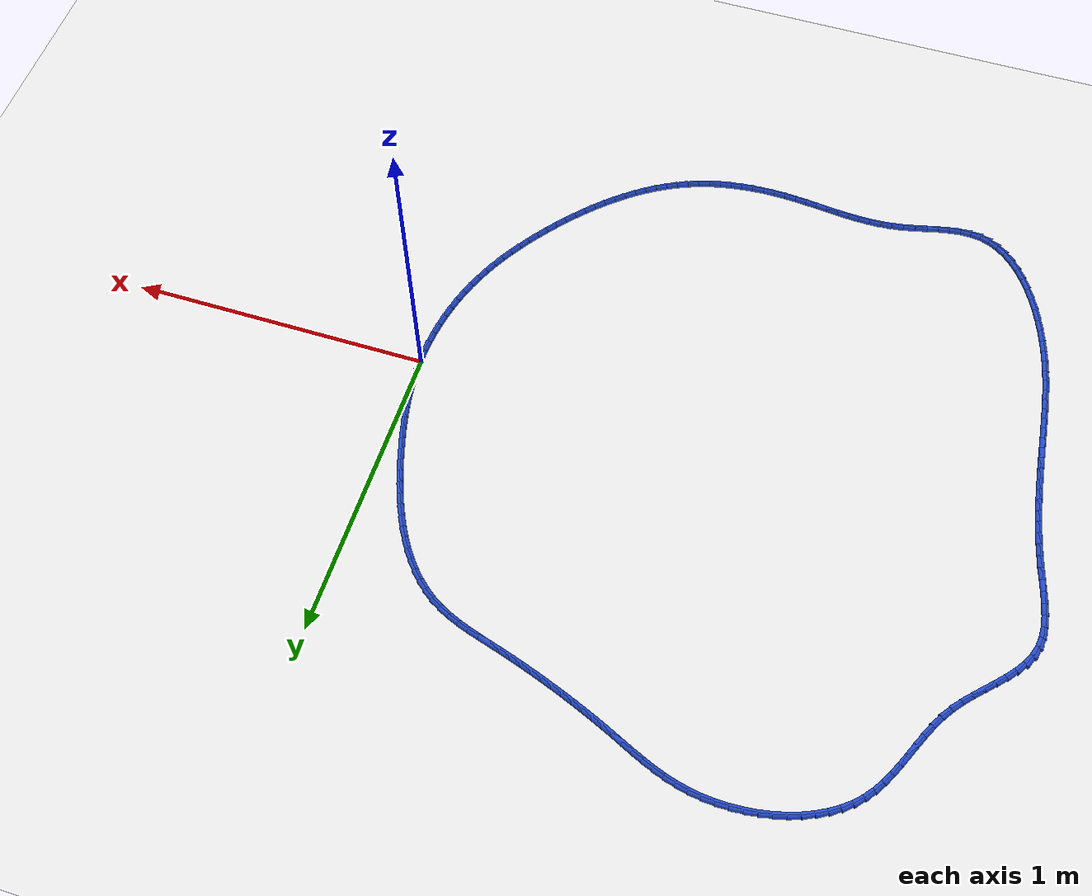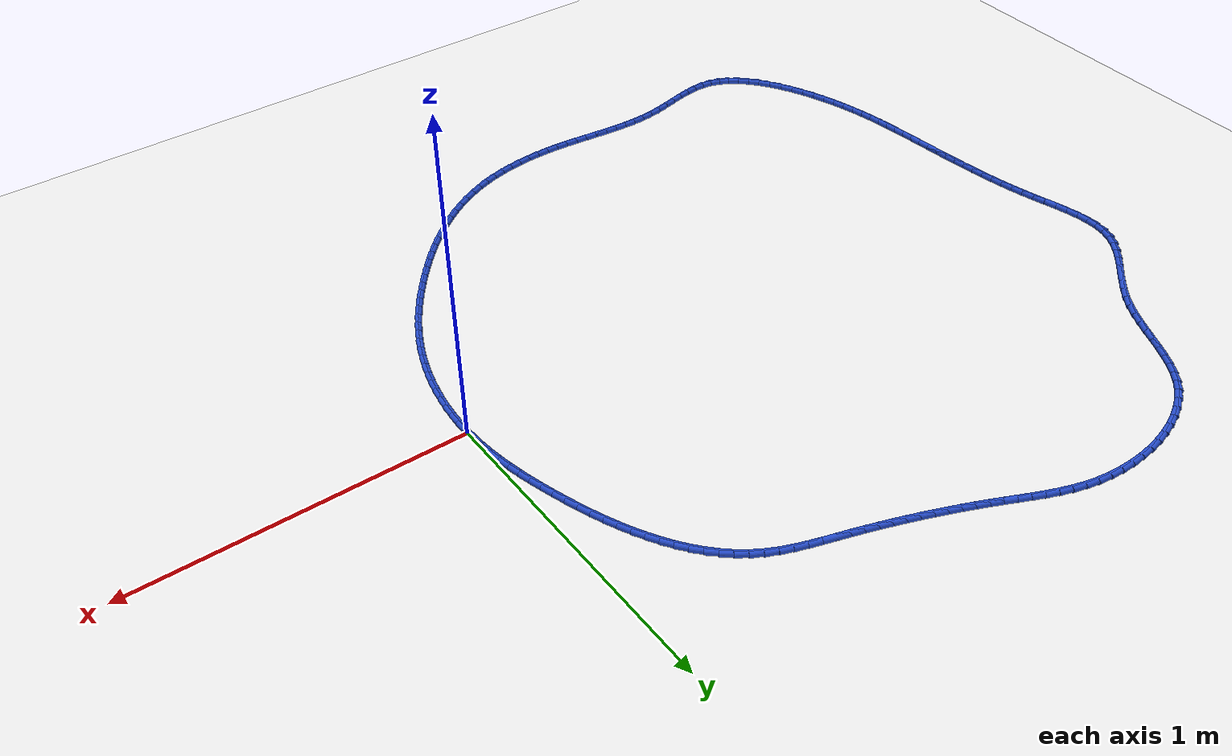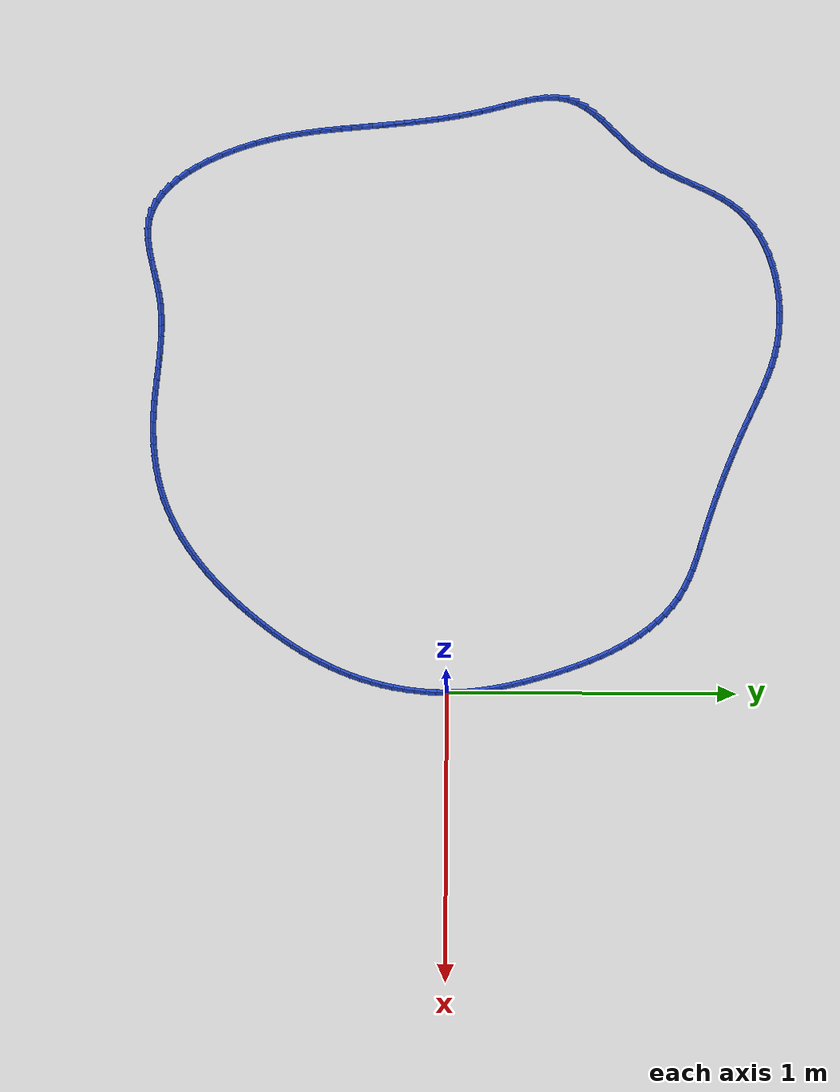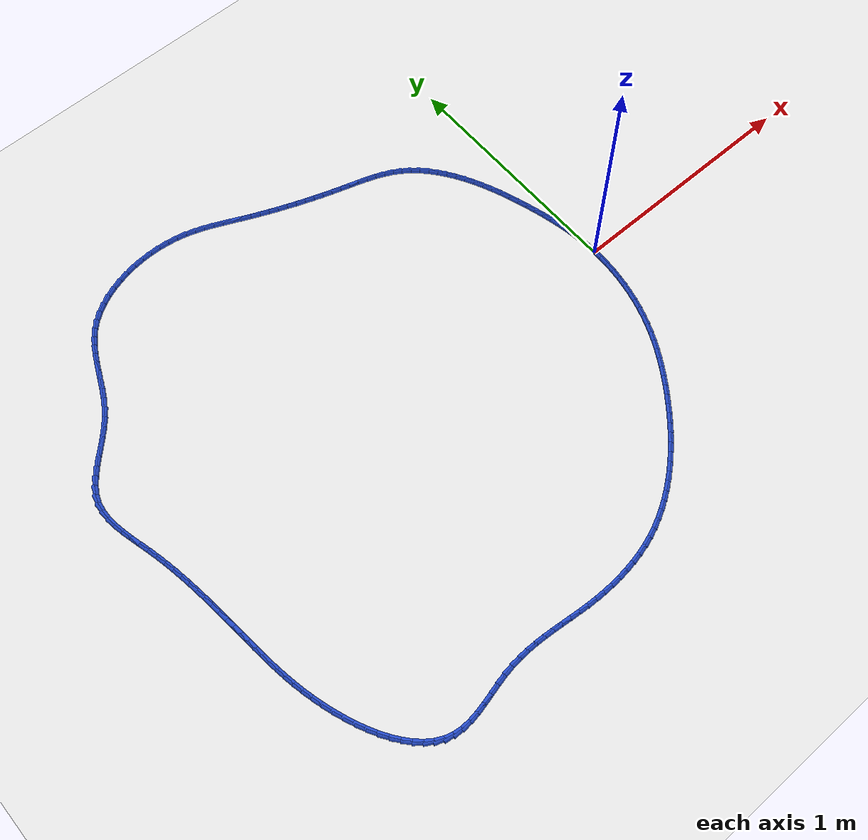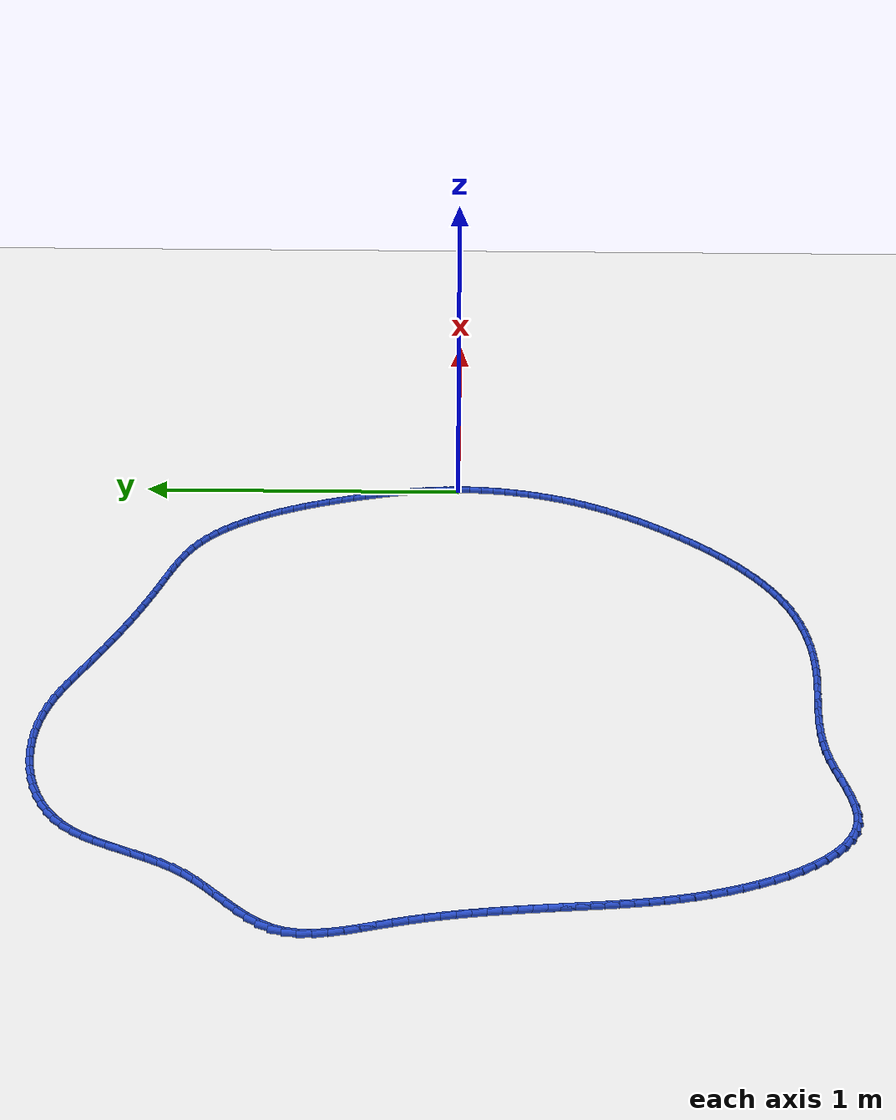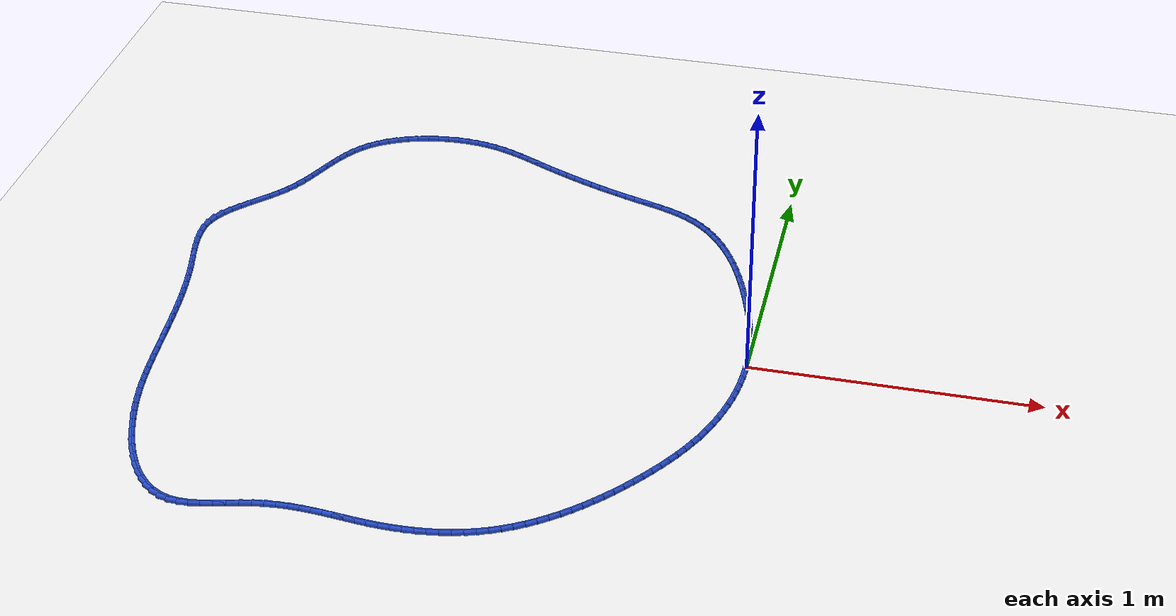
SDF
<sdf version="1.6">
 <world name="default">
  <light name="sun" type="directional">
   <pose>0 0 10 0 -0 0</pose>
   <diffuse>0.8 0.8 0.8 1</diffuse>
   <specular>0.2 0.2 0.2 1</specular>
   <attenuation>
    <range>1000</range>
    <constant>0.9</constant>
    <linear>0.01</linear>
    <quadratic>0.001</quadratic>
   </attenuation>
   <direction>-0.5 0.1 -0.9</direction>
  </light>
  <model name="ground_plane">
   <static>1</static>
   <link name="link">
    <collision name="collision">
     <geometry><plane><normal>0 0 1</normal><size>100 100</size></plane></geometry>
     <surface><friction><ode><mu>100</mu><mu2>50</mu2></ode></friction></surface>
    </collision>
    <visual name="visual">
     <cast_shadows>0</cast_shadows>
     <geometry><plane><normal>0 0 1</normal><size>100 100</size></plane></geometry>
     <material>
      <script><uri>file://media/materials/scripts/gazebo.material</uri><name>Gazebo/WhiteGlow</name></script>
     </material>
    </visual>
   </link>
  </model>
  <gravity>0 0 -9.8</gravity>
  <magnetic_field>6e-06 2.3e-05 -4.2e-05</magnetic_field>
  <atmosphere type="adiabatic"/>
  <physics name="default_physics" default="0" type="ode">
   <max_step_size>0.001</max_step_size>
   <real_time_factor>1</real_time_factor>
   <real_time_update_rate>1000</real_time_update_rate>
  </physics>
  <scene><ambient>0.4 0.4 0.4 1</ambient><background>0.7 0.7 0.7 1</background><shadows>1</shadows></scene>
  <spherical_coordinates>
   <surface_model>EARTH_WGS84</surface_model>
   <latitude_deg>0</latitude_deg>
   <longitude_deg>0</longitude_deg>
   <elevation>0</elevation>
   <heading_deg>0</heading_deg>
  </spherical_coordinates>
  <model name="line">
   <link name="link_0">
    <pose>-3.469446951953614e-18 6.938893903907228e-18 0.01 0 1.57 -1.536955382912983</pose>
    <collision name="collision">
     <geometry><cylinder><radius>0.01</radius><length>0.08</length></cylinder></geometry>
    </collision>
    <visual name="visual">
     <material>
      <script><name>Gazebo/Blue</name><uri>file://media/materials/scripts/gazebo.material</uri></script>
     </material>
     <geometry><cylinder><radius>0.01</radius><length>0.08</length></cylinder></geometry>
    </visual>
   </link>
   <link name="link_1">
    <pose>-0.001274864380905431 0.03765786456587818 0.01 0 1.57 -1.4963036334648052</pose>
    <collision name="collision">
     <geometry><cylinder><radius>0.01</radius><length>0.08</length></cylinder></geometry>
    </collision>
    <visual name="visual">
     <material>
      <script><name>Gazebo/Blue</name><uri>file://media/materials/scripts/gazebo.material</uri></script>
     </material>
     <geometry><cylinder><radius>0.01</radius><length>0.08</length></cylinder></geometry>
    </visual>
   </link>
   <link name="link_2">
    <pose>-0.004071234729490556 0.07512725660731503 0.01 0 1.57 -1.4580223129113172</pose>
    <collision name="collision">
     <geometry><cylinder><radius>0.01</radius><length>0.08</length></cylinder></geometry>
    </collision>
    <visual name="visual">
     <material>
      <script><name>Gazebo/Blue</name><uri>file://media/materials/scripts/gazebo.material</uri></script>
     </material>
     <geometry><cylinder><radius>0.01</radius><length>0.08</length></cylinder></geometry>
    </visual>
   </link>
   <link name="link_3">
    <pose>-0.008299824701219576 0.11246430117498292 0.01 0 1.57 -1.4223683651081251</pose>
    <collision name="collision">
     <geometry><cylinder><radius>0.01</radius><length>0.08</length></cylinder></geometry>
    </collision>
    <visual name="visual">
     <material>
      <script><name>Gazebo/Blue</name><uri>file://media/materials/scripts/gazebo.material</uri></script>
     </material>
     <geometry><cylinder><radius>0.01</radius><length>0.08</length></cylinder></geometry>
    </visual>
   </link>
   <link name="link_4">
    <pose>-0.0138713479515567 0.1497251233195543 0.01 0 1.57 -1.3895362017610302</pose>
    <collision name="collision">
     <geometry><cylinder><radius>0.01</radius><length>0.08</length></cylinder></geometry>
    </collision>
    <visual name="visual">
     <material>
      <script><name>Gazebo/Blue</name><uri>file://media/materials/scripts/gazebo.material</uri></script>
     </material>
     <geometry><cylinder><radius>0.01</radius><length>0.08</length></cylinder></geometry>
    </visual>
   </link>
   <link name="link_5">
    <pose>-0.020696518135966104 0.1869658480917014 0.01 0 1.57 -1.3596605390959235</pose>
    <collision name="collision">
     <geometry><cylinder><radius>0.01</radius><length>0.08</length></cylinder></geometry>
    </collision>
    <visual name="visual">
     <material>
      <script><name>Gazebo/Blue</name><uri>file://media/materials/scripts/gazebo.material</uri></script>
     </material>
     <geometry><cylinder><radius>0.01</radius><length>0.08</length></cylinder></geometry>
    </visual>
   </link>
   <link name="link_6">
    <pose>-0.028686048909911978 0.22424260054209655 0.01 0 1.57 -1.3328219866275868</pose>
    <collision name="collision">
     <geometry><cylinder><radius>0.01</radius><length>0.08</length></cylinder></geometry>
    </collision>
    <visual name="visual">
     <material>
      <script><name>Gazebo/Blue</name><uri>file://media/materials/scripts/gazebo.material</uri></script>
     </material>
     <geometry><cylinder><radius>0.01</radius><length>0.08</length></cylinder></geometry>
    </visual>
   </link>
   <link name="link_7">
    <pose>-0.037750653928858555 0.2616115057214123 0.01 0 1.57 -1.3090542865841548</pose>
    <collision name="collision">
     <geometry><cylinder><radius>0.01</radius><length>0.08</length></cylinder></geometry>
    </collision>
    <visual name="visual">
     <material>
      <script><name>Gazebo/Blue</name><uri>file://media/materials/scripts/gazebo.material</uri></script>
     </material>
     <geometry><cylinder><radius>0.01</radius><length>0.08</length></cylinder></geometry>
    </visual>
   </link>
   <link name="link_8">
    <pose>-0.047801046848269996 0.29912868868032083 0.01 0 1.57 -1.2883522224527768</pose>
    <collision name="collision">
     <geometry><cylinder><radius>0.01</radius><length>0.08</length></cylinder></geometry>
    </collision>
    <visual name="visual">
     <material>
      <script><name>Gazebo/Blue</name><uri>file://media/materials/scripts/gazebo.material</uri></script>
     </material>
     <geometry><cylinder><radius>0.01</radius><length>0.08</length></cylinder></geometry>
    </visual>
   </link>
   <link name="link_9">
    <pose>-0.05874794132361052 0.33685027446949467 0.01 0 1.57 -1.2700182677620713</pose>
    <collision name="collision">
     <geometry><cylinder><radius>0.01</radius><length>0.08</length></cylinder></geometry>
    </collision>
    <visual name="visual">
     <material>
      <script><name>Gazebo/Blue</name><uri>file://media/materials/scripts/gazebo.material</uri></script>
     </material>
     <geometry><cylinder><radius>0.01</radius><length>0.08</length></cylinder></geometry>
    </visual>
   </link>
   <link name="link_10">
    <pose>-0.07052051174366726 0.37480317325983403 0.01 0 1.57 -1.2499681049453149</pose>
    <collision name="collision">
     <geometry><cylinder><radius>0.01</radius><length>0.08</length></cylinder></geometry>
    </collision>
    <visual name="visual">
     <material>
      <script><name>Gazebo/Blue</name><uri>file://media/materials/scripts/gazebo.material</uri></script>
     </material>
     <geometry><cylinder><radius>0.01</radius><length>0.08</length></cylinder></geometry>
    </visual>
   </link>
   <link name="link_11">
    <pose>-0.0831596524420396 0.4128374937540238 0.01 0 1.57 -1.2265370548295362</pose>
    <collision name="collision">
     <geometry><cylinder><radius>0.01</radius><length>0.08</length></cylinder></geometry>
    </collision>
    <visual name="visual">
     <material>
      <script><name>Gazebo/Blue</name><uri>file://media/materials/scripts/gazebo.material</uri></script>
     </material>
     <geometry><cylinder><radius>0.01</radius><length>0.08</length></cylinder></geometry>
    </visual>
   </link>
   <link name="link_12">
    <pose>-0.09674806787344287 0.4507371783957881 0.01 0 1.57 -1.1994857653195417</pose>
    <collision name="collision">
     <geometry><cylinder><radius>0.01</radius><length>0.08</length></cylinder></geometry>
    </collision>
    <visual name="visual">
     <material>
      <script><name>Gazebo/Blue</name><uri>file://media/materials/scripts/gazebo.material</uri></script>
     </material>
     <geometry><cylinder><radius>0.01</radius><length>0.08</length></cylinder></geometry>
    </visual>
   </link>
   <link name="link_13">
    <pose>-0.11136853550880511 0.48828605407765174 0.01 0 1.57 -1.168513662584217</pose>
    <collision name="collision">
     <geometry><cylinder><radius>0.01</radius><length>0.08</length></cylinder></geometry>
    </collision>
    <visual name="visual">
     <material>
      <script><name>Gazebo/Blue</name><uri>file://media/materials/scripts/gazebo.material</uri></script>
     </material>
     <geometry><cylinder><radius>0.01</radius><length>0.08</length></cylinder></geometry>
    </visual>
   </link>
   <link name="link_14">
    <pose>-0.1271038328190542 0.5252679476921395 0.01 0 1.57 -1.1332585287219106</pose>
    <collision name="collision">
     <geometry><cylinder><radius>0.01</radius><length>0.08</length></cylinder></geometry>
    </collision>
    <visual name="visual">
     <material>
      <script><name>Gazebo/Blue</name><uri>file://media/materials/scripts/gazebo.material</uri></script>
     </material>
     <geometry><cylinder><radius>0.01</radius><length>0.08</length></cylinder></geometry>
    </visual>
   </link>
   <link name="link_15">
    <pose>-0.1440367372751182 0.5614666861317759 0.01 0 1.57 -1.093300841316496</pose>
    <collision name="collision">
     <geometry><cylinder><radius>0.01</radius><length>0.08</length></cylinder></geometry>
    </collision>
    <visual name="visual">
     <material>
      <script><name>Gazebo/Blue</name><uri>file://media/materials/scripts/gazebo.material</uri></script>
     </material>
     <geometry><cylinder><radius>0.01</radius><length>0.08</length></cylinder></geometry>
    </visual>
   </link>
   <link name="link_16">
    <pose>-0.16225002634792493 0.596666096289086 0.01 0 1.57 -1.0481728488996482</pose>
    <collision name="collision">
     <geometry><cylinder><radius>0.01</radius><length>0.08</length></cylinder></geometry>
    </collision>
    <visual name="visual">
     <material>
      <script><name>Gazebo/Blue</name><uri>file://media/materials/scripts/gazebo.material</uri></script>
     </material>
     <geometry><cylinder><radius>0.01</radius><length>0.08</length></cylinder></geometry>
    </visual>
   </link>
   <link name="link_17">
    <pose>-0.18182647750840247 0.6306500050565942 0.01 0 1.57 -0.9973759017304041</pose>
    <collision name="collision">
     <geometry><cylinder><radius>0.01</radius><length>0.08</length></cylinder></geometry>
    </collision>
    <visual name="visual">
     <material>
      <script><name>Gazebo/Blue</name><uri>file://media/materials/scripts/gazebo.material</uri></script>
     </material>
     <geometry><cylinder><radius>0.01</radius><length>0.08</length></cylinder></geometry>
    </visual>
   </link>
   <link name="link_18">
    <pose>-0.2028488682274788 0.6632022393268256 0.01 0 1.57 -0.9404105719356979</pose>
    <collision name="collision">
     <geometry><cylinder><radius>0.01</radius><length>0.08</length></cylinder></geometry>
    </collision>
    <visual name="visual">
     <material>
      <script><name>Gazebo/Blue</name><uri>file://media/materials/scripts/gazebo.material</uri></script>
     </material>
     <geometry><cylinder><radius>0.01</radius><length>0.08</length></cylinder></geometry>
    </visual>
   </link>
   <link name="link_19">
    <pose>-0.2253999759760818 0.6941066259923051 0.01 0 1.57 -0.8768247417876714</pose>
    <collision name="collision">
     <geometry><cylinder><radius>0.01</radius><length>0.08</length></cylinder></geometry>
    </collision>
    <visual name="visual">
     <material>
      <script><name>Gazebo/Blue</name><uri>file://media/materials/scripts/gazebo.material</uri></script>
     </material>
     <geometry><cylinder><radius>0.01</radius><length>0.08</length></cylinder></geometry>
    </visual>
   </link>
   <link name="link_20">
    <pose>-0.24956257822513955 0.7231469919455572 0.01 0 1.57 -0.8062841756926488</pose>
    <collision name="collision">
     <geometry><cylinder><radius>0.01</radius><length>0.08</length></cylinder></geometry>
    </collision>
    <visual name="visual">
     <material>
      <script><name>Gazebo/Blue</name><uri>file://media/materials/scripts/gazebo.material</uri></script>
     </material>
     <geometry><cylinder><radius>0.01</radius><length>0.08</length></cylinder></geometry>
    </visual>
   </link>
   <link name="link_21">
    <pose>-0.2754194524455799 0.750107164079107 0.01 0 1.57 -0.7286666107053498</pose>
    <collision name="collision">
     <geometry><cylinder><radius>0.01</radius><length>0.08</length></cylinder></geometry>
    </collision>
    <visual name="visual">
     <material>
      <script><name>Gazebo/Blue</name><uri>file://media/materials/scripts/gazebo.material</uri></script>
     </material>
     <geometry><cylinder><radius>0.01</radius><length>0.08</length></cylinder></geometry>
    </visual>
   </link>
   <link name="link_22">
    <pose>-0.30305337610833094 0.7747709692854787 0.01 0 1.57 -0.6441724190321081</pose>
    <collision name="collision">
     <geometry><cylinder><radius>0.01</radius><length>0.08</length></cylinder></geometry>
    </collision>
    <visual name="visual">
     <material>
      <script><name>Gazebo/Blue</name><uri>file://media/materials/scripts/gazebo.material</uri></script>
     </material>
     <geometry><cylinder><radius>0.01</radius><length>0.08</length></cylinder></geometry>
    </visual>
   </link>
   <link name="link_23">
    <pose>-0.3325471266843205 0.796922234457198 0.01 0 1.57 -0.553586746652375</pose>
    <collision name="collision">
     <geometry><cylinder><radius>0.01</radius><length>0.08</length></cylinder></geometry>
    </collision>
    <visual name="visual">
     <material>
      <script><name>Gazebo/Blue</name><uri>file://media/materials/scripts/gazebo.material</uri></script>
     </material>
     <geometry><cylinder><radius>0.01</radius><length>0.08</length></cylinder></geometry>
    </visual>
   </link>
   <link name="link_24">
    <pose>-0.3639804965695306 0.8163496635535437 0.01 0 1.57 -0.46678511806596856</pose>
    <collision name="collision">
     <geometry><cylinder><radius>0.01</radius><length>0.08</length></cylinder></geometry>
    </collision>
    <visual name="visual">
     <material>
      <script><name>Gazebo/Blue</name><uri>file://media/materials/scripts/gazebo.material</uri></script>
     </material>
     <geometry><cylinder><radius>0.01</radius><length>0.08</length></cylinder></geometry>
    </visual>
   </link>
   <link name="link_25">
    <pose>-0.3972623043759716 0.8331213004408248 0.01 0 1.57 -0.3976859549420545</pose>
    <collision name="collision">
     <geometry><cylinder><radius>0.01</radius><length>0.08</length></cylinder></geometry>
    </collision>
    <visual name="visual">
     <material>
      <script><name>Gazebo/Blue</name><uri>file://media/materials/scripts/gazebo.material</uri></script>
     </material>
     <geometry><cylinder><radius>0.01</radius><length>0.08</length></cylinder></geometry>
    </visual>
   </link>
   <link name="link_26">
    <pose>-0.43204093169635965 0.8477306954639796 0.01 0 1.57 -0.34683090474144274</pose>
    <collision name="collision">
     <geometry><cylinder><radius>0.01</radius><length>0.08</length></cylinder></geometry>
    </collision>
    <visual name="visual">
     <material>
      <script><name>Gazebo/Blue</name><uri>file://media/materials/scripts/gazebo.material</uri></script>
     </material>
     <geometry><cylinder><radius>0.01</radius><length>0.08</length></cylinder></geometry>
    </visual>
   </link>
   <link name="link_27">
    <pose>-0.4679428829486655 0.8607071422720803 0.01 0 1.57 -0.3132682926825116</pose>
    <collision name="collision">
     <geometry><cylinder><radius>0.01</radius><length>0.08</length></cylinder></geometry>
    </collision>
    <visual name="visual">
     <material>
      <script><name>Gazebo/Blue</name><uri>file://media/materials/scripts/gazebo.material</uri></script>
     </material>
     <geometry><cylinder><radius>0.01</radius><length>0.08</length></cylinder></geometry>
    </visual>
   </link>
   <link name="link_28">
    <pose>-0.5045946625508607 0.8725799345141997 0.01 0 1.57 -0.2961576183353673</pose>
    <collision name="collision">
     <geometry><cylinder><radius>0.01</radius><length>0.08</length></cylinder></geometry>
    </collision>
    <visual name="visual">
     <material>
      <script><name>Gazebo/Blue</name><uri>file://media/materials/scripts/gazebo.material</uri></script>
     </material>
     <geometry><cylinder><radius>0.01</radius><length>0.08</length></cylinder></geometry>
    </visual>
   </link>
   <link name="link_29">
    <pose>-0.5416227749209156 0.8838783658394096 0.01 0 1.57 -0.29500936436673536</pose>
    <collision name="collision">
     <geometry><cylinder><radius>0.01</radius><length>0.08</length></cylinder></geometry>
    </collision>
    <visual name="visual">
     <material>
      <script><name>Gazebo/Blue</name><uri>file://media/materials/scripts/gazebo.material</uri></script>
     </material>
     <geometry><cylinder><radius>0.01</radius><length>0.08</length></cylinder></geometry>
    </visual>
   </link>
   <link name="link_30">
    <pose>-0.5786540419581925 0.895131295764723 0.01 0 1.57 -0.30557703463894126</pose>
    <collision name="collision">
     <geometry><cylinder><radius>0.01</radius><length>0.08</length></cylinder></geometry>
    </collision>
    <visual name="visual">
     <material>
      <script><name>Gazebo/Blue</name><uri>file://media/materials/scripts/gazebo.material</uri></script>
     </material>
     <geometry><cylinder><radius>0.01</radius><length>0.08</length></cylinder></geometry>
    </visual>
   </link>
   <link name="link_31">
    <pose>-0.6154170284043116 0.9067284580790453 0.01 0 1.57 -0.317720188088383</pose>
    <collision name="collision">
     <geometry><cylinder><radius>0.01</radius><length>0.08</length></cylinder></geometry>
    </collision>
    <visual name="visual">
     <material>
      <script><name>Gazebo/Blue</name><uri>file://media/materials/scripts/gazebo.material</uri></script>
     </material>
     <geometry><cylinder><radius>0.01</radius><length>0.08</length></cylinder></geometry>
    </visual>
   </link>
   <link name="link_32">
    <pose>-0.6518871339176554 0.9187220582817824 0.01 0 1.57 -0.32990864279539034</pose>
    <collision name="collision">
     <geometry><cylinder><radius>0.01</radius><length>0.08</length></cylinder></geometry>
    </collision>
    <visual name="visual">
     <material>
      <script><name>Gazebo/Blue</name><uri>file://media/materials/scripts/gazebo.material</uri></script>
     </material>
     <geometry><cylinder><radius>0.01</radius><length>0.08</length></cylinder></geometry>
    </visual>
   </link>
   <link name="link_33">
    <pose>-0.6880764637261672 0.9311141097509332 0.01 0 1.57 -0.3421276375032239</pose>
    <collision name="collision">
     <geometry><cylinder><radius>0.01</radius><length>0.08</length></cylinder></geometry>
    </collision>
    <visual name="visual">
     <material>
      <script><name>Gazebo/Blue</name><uri>file://media/materials/scripts/gazebo.material</uri></script>
     </material>
     <geometry><cylinder><radius>0.01</radius><length>0.08</length></cylinder></geometry>
    </visual>
   </link>
   <link name="link_34">
    <pose>-0.7239971230577906 0.9439066258644973 0.01 0 1.57 -0.35436214498259655</pose>
    <collision name="collision">
     <geometry><cylinder><radius>0.01</radius><length>0.08</length></cylinder></geometry>
    </collision>
    <visual name="visual">
     <material>
      <script><name>Gazebo/Blue</name><uri>file://media/materials/scripts/gazebo.material</uri></script>
     </material>
     <geometry><cylinder><radius>0.01</radius><length>0.08</length></cylinder></geometry>
    </visual>
   </link>
   <link name="link_35">
    <pose>-0.7596612171404693 0.9571016200004739 0.01 0 1.57 -0.3665969452555445</pose>
    <collision name="collision">
     <geometry><cylinder><radius>0.01</radius><length>0.08</length></cylinder></geometry>
    </collision>
    <visual name="visual">
     <material>
      <script><name>Gazebo/Blue</name><uri>file://media/materials/scripts/gazebo.material</uri></script>
     </material>
     <geometry><cylinder><radius>0.01</radius><length>0.08</length></cylinder></geometry>
    </visual>
   </link>
   <link name="link_36">
    <pose>-0.7950808512021468 0.9707011055368625 0.01 0 1.57 -0.37881670132085987</pose>
    <collision name="collision">
     <geometry><cylinder><radius>0.01</radius><length>0.08</length></cylinder></geometry>
    </collision>
    <visual name="visual">
     <material>
      <script><name>Gazebo/Blue</name><uri>file://media/materials/scripts/gazebo.material</uri></script>
     </material>
     <geometry><cylinder><radius>0.01</radius><length>0.08</length></cylinder></geometry>
    </visual>
   </link>
   <link name="link_37">
    <pose>-0.8302681304707665 0.9847070958516626 0.01 0 1.57 -0.39100603648781923</pose>
    <collision name="collision">
     <geometry><cylinder><radius>0.01</radius><length>0.08</length></cylinder></geometry>
    </collision>
    <visual name="visual">
     <material>
      <script><name>Gazebo/Blue</name><uri>file://media/materials/scripts/gazebo.material</uri></script>
     </material>
     <geometry><cylinder><radius>0.01</radius><length>0.08</length></cylinder></geometry>
    </visual>
   </link>
   <link name="link_38">
    <pose>-0.8652351601742723 0.9991216043228734 0.01 0 1.57 -0.40314961238867675</pose>
    <collision name="collision">
     <geometry><cylinder><radius>0.01</radius><length>0.08</length></cylinder></geometry>
    </collision>
    <visual name="visual">
     <material>
      <script><name>Gazebo/Blue</name><uri>file://media/materials/scripts/gazebo.material</uri></script>
     </material>
     <geometry><cylinder><radius>0.01</radius><length>0.08</length></cylinder></geometry>
    </visual>
   </link>
   <link name="link_39">
    <pose>-0.8999940455406075 1.0139466443284941 0.01 0 1.57 -0.41523220672429156</pose>
    <collision name="collision">
     <geometry><cylinder><radius>0.01</radius><length>0.08</length></cylinder></geometry>
    </collision>
    <visual name="visual">
     <material>
      <script><name>Gazebo/Blue</name><uri>file://media/materials/scripts/gazebo.material</uri></script>
     </material>
     <geometry><cylinder><radius>0.01</radius><length>0.08</length></cylinder></geometry>
    </visual>
   </link>
   <link name="link_40">
    <pose>-0.934556891797716 1.0291842292465248 0.01 0 1.57 -0.42723747577117693</pose>
    <collision name="collision">
     <geometry><cylinder><radius>0.01</radius><length>0.08</length></cylinder></geometry>
    </collision>
    <visual name="visual">
     <material>
      <script><name>Gazebo/Blue</name><uri>file://media/materials/scripts/gazebo.material</uri></script>
     </material>
     <geometry><cylinder><radius>0.01</radius><length>0.08</length></cylinder></geometry>
    </visual>
   </link>
   <link name="link_41">
    <pose>-0.968935824949788 1.0448363273750696 0.01 0 1.57 -0.4363674215908573</pose>
    <collision name="collision">
     <geometry><cylinder><radius>0.01</radius><length>0.08</length></cylinder></geometry>
    </collision>
    <visual name="visual">
     <material>
      <script><name>Gazebo/Blue</name><uri>file://media/materials/scripts/gazebo.material</uri></script>
     </material>
     <geometry><cylinder><radius>0.01</radius><length>0.08</length></cylinder></geometry>
    </visual>
   </link>
   <link name="link_42">
    <pose>-1.0031869989140767 1.0608093761071757 0.01 0 1.57 -0.4339645834042764</pose>
    <collision name="collision">
     <geometry><cylinder><radius>0.01</radius><length>0.08</length></cylinder></geometry>
    </collision>
    <visual name="visual">
     <material>
      <script><name>Gazebo/Blue</name><uri>file://media/materials/scripts/gazebo.material</uri></script>
     </material>
     <geometry><cylinder><radius>0.01</radius><length>0.08</length></cylinder></geometry>
    </visual>
   </link>
   <link name="link_43">
    <pose>-1.0375035331286517 1.0767126277263728 0.01 0 1.57 -0.4183837993525069</pose>
    <collision name="collision">
     <geometry><cylinder><radius>0.01</radius><length>0.08</length></cylinder></geometry>
    </collision>
    <visual name="visual">
     <material>
      <script><name>Gazebo/Blue</name><uri>file://media/materials/scripts/gazebo.material</uri></script>
     </material>
     <geometry><cylinder><radius>0.01</radius><length>0.08</length></cylinder></geometry>
    </visual>
   </link>
   <link name="link_44">
    <pose>-1.0721051038953961 1.0920977119522464 0.01 0 1.57 -0.3897059963018488</pose>
    <collision name="collision">
     <geometry><cylinder><radius>0.01</radius><length>0.08</length></cylinder></geometry>
    </collision>
    <visual name="visual">
     <material>
      <script><name>Gazebo/Blue</name><uri>file://media/materials/scripts/gazebo.material</uri></script>
     </material>
     <geometry><cylinder><radius>0.01</radius><length>0.08</length></cylinder></geometry>
    </visual>
   </link>
   <link name="link_45">
    <pose>-1.107211387516195 1.1065162585043824 0.01 0 1.57 -0.34813743807292336</pose>
    <collision name="collision">
     <geometry><cylinder><radius>0.01</radius><length>0.08</length></cylinder></geometry>
    </collision>
    <visual name="visual">
     <material>
      <script><name>Gazebo/Blue</name><uri>file://media/materials/scripts/gazebo.material</uri></script>
     </material>
     <geometry><cylinder><radius>0.01</radius><length>0.08</length></cylinder></geometry>
    </visual>
   </link>
   <link name="link_46">
    <pose>-1.1430420602929325 1.1195198971023663 0.01 0 1.57 -0.2941474006051731</pose>
    <collision name="collision">
     <geometry><cylinder><radius>0.01</radius><length>0.08</length></cylinder></geometry>
    </collision>
    <visual name="visual">
     <material>
      <script><name>Gazebo/Blue</name><uri>file://media/materials/scripts/gazebo.material</uri></script>
     </material>
     <geometry><cylinder><radius>0.01</radius><length>0.08</length></cylinder></geometry>
    </visual>
   </link>
   <link name="link_47">
    <pose>-1.1798167985274925 1.1306602574657842 0.01 0 1.57 -0.2286504502082588</pose>
    <collision name="collision">
     <geometry><cylinder><radius>0.01</radius><length>0.08</length></cylinder></geometry>
    </collision>
    <visual name="visual">
     <material>
      <script><name>Gazebo/Blue</name><uri>file://media/materials/scripts/gazebo.material</uri></script>
     </material>
     <geometry><cylinder><radius>0.01</radius><length>0.08</length></cylinder></geometry>
    </visual>
   </link>
   <link name="link_48">
    <pose>-1.2177549380891592 1.139489231731959 0.01 0 1.57 -0.15655266634701503</pose>
    <collision name="collision">
     <geometry><cylinder><radius>0.01</radius><length>0.08</length></cylinder></geometry>
    </collision>
    <visual name="visual">
     <material>
      <script><name>Gazebo/Blue</name><uri>file://media/materials/scripts/gazebo.material</uri></script>
     </material>
     <geometry><cylinder><radius>0.01</radius><length>0.08</length></cylinder></geometry>
    </visual>
   </link>
   <link name="link_49">
    <pose>-1.2569281903784912 1.1456725063081472 0.01 0 1.57 -0.08691703948825712</pose>
    <collision name="collision">
     <geometry><cylinder><radius>0.01</radius><length>0.08</length></cylinder></geometry>
    </collision>
    <visual name="visual">
     <material>
      <script><name>Gazebo/Blue</name><uri>file://media/materials/scripts/gazebo.material</uri></script>
     </material>
     <geometry><cylinder><radius>0.01</radius><length>0.08</length></cylinder></geometry>
    </visual>
   </link>
   <link name="link_50">
    <pose>-1.297030592781641 1.149166892366436 0.01 0 1.57 -0.019871525918372043</pose>
    <collision name="collision">
     <geometry><cylinder><radius>0.01</radius><length>0.08</length></cylinder></geometry>
    </collision>
    <visual name="visual">
     <material>
      <script><name>Gazebo/Blue</name><uri>file://media/materials/scripts/gazebo.material</uri></script>
     </material>
     <geometry><cylinder><radius>0.01</radius><length>0.08</length></cylinder></geometry>
    </visual>
   </link>
   <link name="link_51">
    <pose>-1.3376966445136445 1.1499750952506165 0.01 0 1.57 0.04585823765514985</pose>
    <collision name="collision">
     <geometry><cylinder><radius>0.01</radius><length>0.08</length></cylinder></geometry>
    </collision>
    <visual name="visual">
     <material>
      <script><name>Gazebo/Blue</name><uri>file://media/materials/scripts/gazebo.material</uri></script>
     </material>
     <geometry><cylinder><radius>0.01</radius><length>0.08</length></cylinder></geometry>
    </visual>
   </link>
   <link name="link_52">
    <pose>-1.3785608447895368 1.1480998203044808 0.01 0 1.57 0.11148665976598979</pose>
    <collision name="collision">
     <geometry><cylinder><radius>0.01</radius><length>0.08</length></cylinder></geometry>
    </collision>
    <visual name="visual">
     <material>
      <script><name>Gazebo/Blue</name><uri>file://media/materials/scripts/gazebo.material</uri></script>
     </material>
     <geometry><cylinder><radius>0.01</radius><length>0.08</length></cylinder></geometry>
    </visual>
   </link>
   <link name="link_53">
    <pose>-1.419257692824352 1.1435437728718199 0.01 0 1.57 0.17820376297349944</pose>
    <collision name="collision">
     <geometry><cylinder><radius>0.01</radius><length>0.08</length></cylinder></geometry>
    </collision>
    <visual name="visual">
     <material>
      <script><name>Gazebo/Blue</name><uri>file://media/materials/scripts/gazebo.material</uri></script>
     </material>
     <geometry><cylinder><radius>0.01</radius><length>0.08</length></cylinder></geometry>
    </visual>
   </link>
   <link name="link_54">
    <pose>-1.4594216878331259 1.136309658296426 0.01 0 1.57 0.2472081602341265</pose>
    <collision name="collision">
     <geometry><cylinder><radius>0.01</radius><length>0.08</length></cylinder></geometry>
    </collision>
    <visual name="visual">
     <material>
      <script><name>Gazebo/Blue</name><uri>file://media/materials/scripts/gazebo.material</uri></script>
     </material>
     <geometry><cylinder><radius>0.01</radius><length>0.08</length></cylinder></geometry>
    </visual>
   </link>
   <link name="link_55">
    <pose>-1.4986873290308944 1.126400181922091 0.01 0 1.57 0.31973307414224117</pose>
    <collision name="collision">
     <geometry><cylinder><radius>0.01</radius><length>0.08</length></cylinder></geometry>
    </collision>
    <visual name="visual">
     <material>
      <script><name>Gazebo/Blue</name><uri>file://media/materials/scripts/gazebo.material</uri></script>
     </material>
     <geometry><cylinder><radius>0.01</radius><length>0.08</length></cylinder></geometry>
    </visual>
   </link>
   <link name="link_56">
    <pose>-1.5366891156326905 1.113818049092606 0.01 0 1.57 0.3970590777128254</pose>
    <collision name="collision">
     <geometry><cylinder><radius>0.01</radius><length>0.08</length></cylinder></geometry>
    </collision>
    <visual name="visual">
     <material>
      <script><name>Gazebo/Blue</name><uri>file://media/materials/scripts/gazebo.material</uri></script>
     </material>
     <geometry><cylinder><radius>0.01</radius><length>0.08</length></cylinder></geometry>
    </visual>
   </link>
   <link name="link_57">
    <pose>-1.5730615468535507 1.0985659651517632 0.01 0 1.57 0.4805031585577321</pose>
    <collision name="collision">
     <geometry><cylinder><radius>0.01</radius><length>0.08</length></cylinder></geometry>
    </collision>
    <visual name="visual">
     <material>
      <script><name>Gazebo/Blue</name><uri>file://media/materials/scripts/gazebo.material</uri></script>
     </material>
     <geometry><cylinder><radius>0.01</radius><length>0.08</length></cylinder></geometry>
    </visual>
   </link>
   <link name="link_58">
    <pose>-1.60743912190851 1.0806466354433535 0.01 0 1.57 0.5713678177003826</pose>
    <collision name="collision">
     <geometry><cylinder><radius>0.01</radius><length>0.08</length></cylinder></geometry>
    </collision>
    <visual name="visual">
     <material>
      <script><name>Gazebo/Blue</name><uri>file://media/materials/scripts/gazebo.material</uri></script>
     </material>
     <geometry><cylinder><radius>0.01</radius><length>0.08</length></cylinder></geometry>
    </visual>
   </link>
   <link name="link_59">
    <pose>-1.6394563400126025 1.0600627653111694 0.01 0 1.57 0.6708280116067767</pose>
    <collision name="collision">
     <geometry><cylinder><radius>0.01</radius><length>0.08</length></cylinder></geometry>
    </collision>
    <visual name="visual">
     <material>
      <script><name>Gazebo/Blue</name><uri>file://media/materials/scripts/gazebo.material</uri></script>
     </material>
     <geometry><cylinder><radius>0.01</radius><length>0.08</length></cylinder></geometry>
    </visual>
   </link>
   <link name="link_60">
    <pose>-1.6687477003808644 1.0368170600990019 0.01 0 1.57 0.7797327660083936</pose>
    <collision name="collision">
     <geometry><cylinder><radius>0.01</radius><length>0.08</length></cylinder></geometry>
    </collision>
    <visual name="visual">
     <material>
      <script><name>Gazebo/Blue</name><uri>file://media/materials/scripts/gazebo.material</uri></script>
     </material>
     <geometry><cylinder><radius>0.01</radius><length>0.08</length></cylinder></geometry>
    </visual>
   </link>
   <link name="link_61">
    <pose>-1.694947724044376 1.0109122342720522 0.01 0 1.57 0.8927158887377593</pose>
    <collision name="collision">
     <geometry><cylinder><radius>0.01</radius><length>0.08</length></cylinder></geometry>
    </collision>
    <visual name="visual">
     <material>
      <script><name>Gazebo/Blue</name><uri>file://media/materials/scripts/gazebo.material</uri></script>
     </material>
     <geometry><cylinder><radius>0.01</radius><length>0.08</length></cylinder></geometry>
    </visual>
   </link>
   <link name="link_62">
    <pose>-1.717887389570348 0.9824331422701079 0.01 0 1.57 0.9889415055753171</pose>
    <collision name="collision">
     <geometry><cylinder><radius>0.01</radius><length>0.08</length></cylinder></geometry>
    </collision>
    <visual name="visual">
     <material>
      <script><name>Gazebo/Blue</name><uri>file://media/materials/scripts/gazebo.material</uri></script>
     </material>
     <geometry><cylinder><radius>0.01</radius><length>0.08</length></cylinder></geometry>
    </visual>
   </link>
   <link name="link_63">
    <pose>-1.7380733393709384 0.9517471372965481 0.01 0 1.57 1.0625692841840495</pose>
    <collision name="collision">
     <geometry><cylinder><radius>0.01</radius><length>0.08</length></cylinder></geometry>
    </collision>
    <visual name="visual">
     <material>
      <script><name>Gazebo/Blue</name><uri>file://media/materials/scripts/gazebo.material</uri></script>
     </material>
     <geometry><cylinder><radius>0.01</radius><length>0.08</length></cylinder></geometry>
    </visual>
   </link>
   <link name="link_64">
    <pose>-1.7561573594293498 0.9192822578787773 0.01 0 1.57 1.1136514534009831</pose>
    <collision name="collision">
     <geometry><cylinder><radius>0.01</radius><length>0.08</length></cylinder></geometry>
    </collision>
    <visual name="visual">
     <material>
      <script><name>Gazebo/Blue</name><uri>file://media/materials/scripts/gazebo.material</uri></script>
     </material>
     <geometry><cylinder><radius>0.01</radius><length>0.08</length></cylinder></geometry>
    </visual>
   </link>
   <link name="link_65">
    <pose>-1.7727912357287838 0.8854665425441981 0.01 0 1.57 1.1430889754072613</pose>
    <collision name="collision">
     <geometry><cylinder><radius>0.01</radius><length>0.08</length></cylinder></geometry>
    </collision>
    <visual name="visual">
     <material>
      <script><name>Gazebo/Blue</name><uri>file://media/materials/scripts/gazebo.material</uri></script>
     </material>
     <geometry><cylinder><radius>0.01</radius><length>0.08</length></cylinder></geometry>
    </visual>
   </link>
   <link name="link_66">
    <pose>-1.7886267542524426 0.8507280298202146 0.01 0 1.57 1.1518679548077155</pose>
    <collision name="collision">
     <geometry><cylinder><radius>0.01</radius><length>0.08</length></cylinder></geometry>
    </collision>
    <visual name="visual">
     <material>
      <script><name>Gazebo/Blue</name><uri>file://media/materials/scripts/gazebo.material</uri></script>
     </material>
     <geometry><cylinder><radius>0.01</radius><length>0.08</length></cylinder></geometry>
    </visual>
   </link>
   <link name="link_67">
    <pose>-1.8043157009835278 0.815494758234231 0.01 0 1.57 1.1406829909434208</pose>
    <collision name="collision">
     <geometry><cylinder><radius>0.01</radius><length>0.08</length></cylinder></geometry>
    </collision>
    <visual name="visual">
     <material>
      <script><name>Gazebo/Blue</name><uri>file://media/materials/scripts/gazebo.material</uri></script>
     </material>
     <geometry><cylinder><radius>0.01</radius><length>0.08</length></cylinder></geometry>
    </visual>
   </link>
   <link name="link_68">
    <pose>-1.8205098619052416 0.7801947663136507 0.01 0 1.57 1.1098582787186067</pose>
    <collision name="collision">
     <geometry><cylinder><radius>0.01</radius><length>0.08</length></cylinder></geometry>
    </collision>
    <visual name="visual">
     <material>
      <script><name>Gazebo/Blue</name><uri>file://media/materials/scripts/gazebo.material</uri></script>
     </material>
     <geometry><cylinder><radius>0.01</radius><length>0.08</length></cylinder></geometry>
    </visual>
   </link>
   <link name="link_69">
    <pose>-1.8378610230007868 0.7452560925858771 0.01 0 1.57 1.0594984990624667</pose>
    <collision name="collision">
     <geometry><cylinder><radius>0.01</radius><length>0.08</length></cylinder></geometry>
    </collision>
    <visual name="visual">
     <material>
      <script><name>Gazebo/Blue</name><uri>file://media/materials/scripts/gazebo.material</uri></script>
     </material>
     <geometry><cylinder><radius>0.01</radius><length>0.08</length></cylinder></geometry>
    </visual>
   </link>
   <link name="link_70">
    <pose>-1.8570209702533635 0.7111067755783148 0.01 0 1.57 0.9898501246671527</pose>
    <collision name="collision">
     <geometry><cylinder><radius>0.01</radius><length>0.08</length></cylinder></geometry>
    </collision>
    <visual name="visual">
     <material>
      <script><name>Gazebo/Blue</name><uri>file://media/materials/scripts/gazebo.material</uri></script>
     </material>
     <geometry><cylinder><radius>0.01</radius><length>0.08</length></cylinder></geometry>
    </visual>
   </link>
   <link name="link_71">
    <pose>-1.8786414896461752 0.6781748538183666 0.01 0 1.57 0.9072563515920239</pose>
    <collision name="collision">
     <geometry><cylinder><radius>0.01</radius><length>0.08</length></cylinder></geometry>
    </collision>
    <visual name="visual">
     <material>
      <script><name>Gazebo/Blue</name><uri>file://media/materials/scripts/gazebo.material</uri></script>
     </material>
     <geometry><cylinder><radius>0.01</radius><length>0.08</length></cylinder></geometry>
    </visual>
   </link>
   <link name="link_72">
    <pose>-1.9031762773637642 0.6467921298833953 0.01 0 1.57 0.8433022599514356</pose>
    <collision name="collision">
     <geometry><cylinder><radius>0.01</radius><length>0.08</length></cylinder></geometry>
    </collision>
    <visual name="visual">
     <material>
      <script><name>Gazebo/Blue</name><uri>file://media/materials/scripts/gazebo.material</uri></script>
     </material>
     <geometry><cylinder><radius>0.01</radius><length>0.08</length></cylinder></geometry>
    </visual>
   </link>
   <link name="link_73">
    <pose>-1.929938443048343 0.6167362868037252 0.01 0 1.57 0.8073765648505122</pose>
    <collision name="collision">
     <geometry><cylinder><radius>0.01</radius><length>0.08</length></cylinder></geometry>
    </collision>
    <visual name="visual">
     <material>
      <script><name>Gazebo/Blue</name><uri>file://media/materials/scripts/gazebo.material</uri></script>
     </material>
     <geometry><cylinder><radius>0.01</radius><length>0.08</length></cylinder></geometry>
    </visual>
   </link>
   <link name="link_74">
    <pose>-1.957833697035474 0.5875870849524439 0.01 0 1.57 0.7982869700072771</pose>
    <collision name="collision">
     <geometry><cylinder><radius>0.01</radius><length>0.08</length></cylinder></geometry>
    </collision>
    <visual name="visual">
     <material>
      <script><name>Gazebo/Blue</name><uri>file://media/materials/scripts/gazebo.material</uri></script>
     </material>
     <geometry><cylinder><radius>0.01</radius><length>0.08</length></cylinder></geometry>
    </visual>
   </link>
   <link name="link_75">
    <pose>-1.9857672413259768 0.5589240377435494 0.01 0 1.57 0.8163996865701358</pose>
    <collision name="collision">
     <geometry><cylinder><radius>0.01</radius><length>0.08</length></cylinder></geometry>
    </collision>
    <visual name="visual">
     <material>
      <script><name>Gazebo/Blue</name><uri>file://media/materials/scripts/gazebo.material</uri></script>
     </material>
     <geometry><cylinder><radius>0.01</radius><length>0.08</length></cylinder></geometry>
    </visual>
   </link>
   <link name="link_76">
    <pose>-2.0126442779206717 0.5303266585910381 0.01 0 1.57 0.8639735687824688</pose>
    <collision name="collision">
     <geometry><cylinder><radius>0.01</radius><length>0.08</length></cylinder></geometry>
    </collision>
    <visual name="visual">
     <material>
      <script><name>Gazebo/Blue</name><uri>file://media/materials/scripts/gazebo.material</uri></script>
     </material>
     <geometry><cylinder><radius>0.01</radius><length>0.08</length></cylinder></geometry>
    </visual>
   </link>
   <link name="link_77">
    <pose>-2.037370008820381 0.5013744609089071 0.01 0 1.57 0.9450954609293862</pose>
    <collision name="collision">
     <geometry><cylinder><radius>0.01</radius><length>0.08</length></cylinder></geometry>
    </collision>
    <visual name="visual">
     <material>
      <script><name>Gazebo/Blue</name><uri>file://media/materials/scripts/gazebo.material</uri></script>
     </material>
     <geometry><cylinder><radius>0.01</radius><length>0.08</length></cylinder></geometry>
    </visual>
   </link>
   <link name="link_78">
    <pose>-2.0588496360259256 0.4716469581111541 0.01 0 1.57 1.0647086450625842</pose>
    <collision name="collision">
     <geometry><cylinder><radius>0.01</radius><length>0.08</length></cylinder></geometry>
    </collision>
    <visual name="visual">
     <material>
      <script><name>Gazebo/Blue</name><uri>file://media/materials/scripts/gazebo.material</uri></script>
     </material>
     <geometry><cylinder><radius>0.01</radius><length>0.08</length></cylinder></geometry>
    </visual>
   </link>
   <link name="link_79">
    <pose>-2.075988361538125 0.4407236636117757 0.01 0 1.57 1.2255189261155242</pose>
    <collision name="collision">
     <geometry><cylinder><radius>0.01</radius><length>0.08</length></cylinder></geometry>
    </collision>
    <visual name="visual">
     <material>
      <script><name>Gazebo/Blue</name><uri>file://media/materials/scripts/gazebo.material</uri></script>
     </material>
     <geometry><cylinder><radius>0.01</radius><length>0.08</length></cylinder></geometry>
    </visual>
   </link>
   <link name="link_80">
    <pose>-2.0876922735749788 0.4081843972435069 0.01 0 1.57 1.406924404670239</pose>
    <collision name="collision">
     <geometry><cylinder><radius>0.01</radius><length>0.08</length></cylinder></geometry>
    </collision>
    <visual name="visual">
     <material>
      <script><name>Gazebo/Blue</name><uri>file://media/materials/scripts/gazebo.material</uri></script>
     </material>
     <geometry><cylinder><radius>0.01</radius><length>0.08</length></cylinder></geometry>
    </visual>
   </link>
   <link name="link_81">
    <pose>-2.093380169200939 0.37378625321567344 0.01 0 1.57 1.5579517132813043</pose>
    <collision name="collision">
     <geometry><cylinder><radius>0.01</radius><length>0.08</length></cylinder></geometry>
    </collision>
    <visual name="visual">
     <material>
      <script><name>Gazebo/Blue</name><uri>file://media/materials/scripts/gazebo.material</uri></script>
     </material>
     <geometry><cylinder><radius>0.01</radius><length>0.08</length></cylinder></geometry>
    </visual>
   </link>
   <link name="link_82">
    <pose>-2.0938429284752664 0.3377607375976978 0.01 0 1.57 -1.4708594749327406</pose>
    <collision name="collision">
     <geometry><cylinder><radius>0.01</radius><length>0.08</length></cylinder></geometry>
    </collision>
    <visual name="visual">
     <material>
      <script><name>Gazebo/Blue</name><uri>file://media/materials/scripts/gazebo.material</uri></script>
     </material>
     <geometry><cylinder><radius>0.01</radius><length>0.08</length></cylinder></geometry>
    </visual>
   </link>
   <link name="link_83">
    <pose>-2.0900985266557304 0.30041787696829464 0.01 0 1.57 -1.391931752499028</pose>
    <collision name="collision">
     <geometry><cylinder><radius>0.01</radius><length>0.08</length></cylinder></geometry>
    </collision>
    <visual name="visual">
     <material>
      <script><name>Gazebo/Blue</name><uri>file://media/materials/scripts/gazebo.material</uri></script>
     </material>
     <geometry><cylinder><radius>0.01</radius><length>0.08</length></cylinder></geometry>
    </visual>
   </link>
   <link name="link_84">
    <pose>-2.0831649390001017 0.26206769790618006 0.01 0 1.57 -1.3417168836739684</pose>
    <collision name="collision">
     <geometry><cylinder><radius>0.01</radius><length>0.08</length></cylinder></geometry>
    </collision>
    <visual name="visual">
     <material>
      <script><name>Gazebo/Blue</name><uri>file://media/materials/scripts/gazebo.material</uri></script>
     </material>
     <geometry><cylinder><radius>0.01</radius><length>0.08</length></cylinder></geometry>
    </visual>
   </link>
   <link name="link_85">
    <pose>-2.074060140766149 0.22302022699006852 0.01 0 1.57 -1.3163094576026793</pose>
    <collision name="collision">
     <geometry><cylinder><radius>0.01</radius><length>0.08</length></cylinder></geometry>
    </collision>
    <visual name="visual">
     <material>
      <script><name>Gazebo/Blue</name><uri>file://media/materials/scripts/gazebo.material</uri></script>
     </material>
     <geometry><cylinder><radius>0.01</radius><length>0.08</length></cylinder></geometry>
    </visual>
   </link>
   <link name="link_86">
    <pose>-2.0638021072116444 0.183585490798676 0.01 0 1.57 -1.3135813652366208</pose>
    <collision name="collision">
     <geometry><cylinder><radius>0.01</radius><length>0.08</length></cylinder></geometry>
    </collision>
    <visual name="visual">
     <material>
      <script><name>Gazebo/Blue</name><uri>file://media/materials/scripts/gazebo.material</uri></script>
     </material>
     <geometry><cylinder><radius>0.01</radius><length>0.08</length></cylinder></geometry>
    </visual>
   </link>
   <link name="link_87">
    <pose>-2.0534088135943556 0.14407351591071751 0.01 0 1.57 -1.331469023888554</pose>
    <collision name="collision">
     <geometry><cylinder><radius>0.01</radius><length>0.08</length></cylinder></geometry>
    </collision>
    <visual name="visual">
     <material>
      <script><name>Gazebo/Blue</name><uri>file://media/materials/scripts/gazebo.material</uri></script>
     </material>
     <geometry><cylinder><radius>0.01</radius><length>0.08</length></cylinder></geometry>
    </visual>
   </link>
   <link name="link_88">
    <pose>-2.043818918724588 0.1047712862159255 0.01 0 1.57 -1.3554118695033952</pose>
    <collision name="collision">
     <geometry><cylinder><radius>0.01</radius><length>0.08</length></cylinder></geometry>
    </collision>
    <visual name="visual">
     <material>
      <script><name>Gazebo/Blue</name><uri>file://media/materials/scripts/gazebo.material</uri></script>
     </material>
     <geometry><cylinder><radius>0.01</radius><length>0.08</length></cylinder></geometry>
    </visual>
   </link>
   <link name="link_89">
    <pose>-2.0352855564971084 0.06576662971741916 0.01 0 1.57 -1.377616037008083</pose>
    <collision name="collision">
     <geometry><cylinder><radius>0.01</radius><length>0.08</length></cylinder></geometry>
    </collision>
    <visual name="visual">
     <material>
      <script><name>Gazebo/Blue</name><uri>file://media/materials/scripts/gazebo.material</uri></script>
     </material>
     <geometry><cylinder><radius>0.01</radius><length>0.08</length></cylinder></geometry>
    </visual>
   </link>
   <link name="link_90">
    <pose>-2.027710921956295 0.027045421102961317 0.01 0 1.57 -1.397870445047492</pose>
    <collision name="collision">
     <geometry><cylinder><radius>0.01</radius><length>0.08</length></cylinder></geometry>
    </collision>
    <visual name="visual">
     <material>
      <script><name>Gazebo/Blue</name><uri>file://media/materials/scripts/gazebo.material</uri></script>
     </material>
     <geometry><cylinder><radius>0.01</radius><length>0.08</length></cylinder></geometry>
    </visual>
   </link>
   <link name="link_91">
    <pose>-2.0209943699664557 -0.011407290057148188 0.01 0 1.57 -1.41604248684984</pose>
    <collision name="collision">
     <geometry><cylinder><radius>0.01</radius><length>0.08</length></cylinder></geometry>
    </collision>
    <visual name="visual">
     <material>
      <script><name>Gazebo/Blue</name><uri>file://media/materials/scripts/gazebo.material</uri></script>
     </material>
     <geometry><cylinder><radius>0.01</radius><length>0.08</length></cylinder></geometry>
    </visual>
   </link>
   <link name="link_92">
    <pose>-2.0150352553918998 -0.049606454192610325 0.01 0 1.57 -1.4320145003433264</pose>
    <collision name="collision">
     <geometry><cylinder><radius>0.01</radius><length>0.08</length></cylinder></geometry>
    </collision>
    <visual name="visual">
     <material>
      <script><name>Gazebo/Blue</name><uri>file://media/materials/scripts/gazebo.material</uri></script>
     </material>
     <geometry><cylinder><radius>0.01</radius><length>0.08</length></cylinder></geometry>
    </visual>
   </link>
   <link name="link_93">
    <pose>-2.0097329330969367 -0.0875670217331237 0.01 0 1.57 -1.4456831838771984</pose>
    <collision name="collision">
     <geometry><cylinder><radius>0.01</radius><length>0.08</length></cylinder></geometry>
    </collision>
    <visual name="visual">
     <material>
      <script><name>Gazebo/Blue</name><uri>file://media/materials/scripts/gazebo.material</uri></script>
     </material>
     <geometry><cylinder><radius>0.01</radius><length>0.08</length></cylinder></geometry>
    </visual>
   </link>
   <link name="link_94">
    <pose>-2.004986757945876 -0.1253039431083893 0.01 0 1.57 -1.4569587348513444</pose>
    <collision name="collision">
     <geometry><cylinder><radius>0.01</radius><length>0.08</length></cylinder></geometry>
    </collision>
    <visual name="visual">
     <material>
      <script><name>Gazebo/Blue</name><uri>file://media/materials/scripts/gazebo.material</uri></script>
     </material>
     <geometry><cylinder><radius>0.01</radius><length>0.08</length></cylinder></geometry>
    </visual>
   </link>
   <link name="link_95">
    <pose>-2.000696084803027 -0.16283216874810735 0.01 0 1.57 -1.4657638605885397</pose>
    <collision name="collision">
     <geometry><cylinder><radius>0.01</radius><length>0.08</length></cylinder></geometry>
    </collision>
    <visual name="visual">
     <material>
      <script><name>Gazebo/Blue</name><uri>file://media/materials/scripts/gazebo.material</uri></script>
     </material>
     <geometry><cylinder><radius>0.01</radius><length>0.08</length></cylinder></geometry>
    </visual>
   </link>
   <link name="link_96">
    <pose>-1.9967602685326975 -0.20016664908197793 0.01 0 1.57 -1.4720328054855951</pose>
    <collision name="collision">
     <geometry><cylinder><radius>0.01</radius><length>0.08</length></cylinder></geometry>
    </collision>
    <visual name="visual">
     <material>
      <script><name>Gazebo/Blue</name><uri>file://media/materials/scripts/gazebo.material</uri></script>
     </material>
     <geometry><cylinder><radius>0.01</radius><length>0.08</length></cylinder></geometry>
    </visual>
   </link>
   <link name="link_97">
    <pose>-1.9930786639991978 -0.2373223345397013 0.01 0 1.57 -1.4757105260484507</pose>
    <collision name="collision">
     <geometry><cylinder><radius>0.01</radius><length>0.08</length></cylinder></geometry>
    </collision>
    <visual name="visual">
     <material>
      <script><name>Gazebo/Blue</name><uri>file://media/materials/scripts/gazebo.material</uri></script>
     </material>
     <geometry><cylinder><radius>0.01</radius><length>0.08</length></cylinder></geometry>
    </visual>
   </link>
   <link name="link_98">
    <pose>-1.9895506260668374 -0.27431417555097837 0.01 0 1.57 -1.4767521283822562</pose>
    <collision name="collision">
     <geometry><cylinder><radius>0.01</radius><length>0.08</length></cylinder></geometry>
    </collision>
    <visual name="visual">
     <material>
      <script><name>Gazebo/Blue</name><uri>file://media/materials/scripts/gazebo.material</uri></script>
     </material>
     <geometry><cylinder><radius>0.01</radius><length>0.08</length></cylinder></geometry>
    </visual>
   </link>
   <link name="link_99">
    <pose>-1.9860755095999243 -0.31115712254550776 0.01 0 1.57 -1.475122662773297</pose>
    <collision name="collision">
     <geometry><cylinder><radius>0.01</radius><length>0.08</length></cylinder></geometry>
    </collision>
    <visual name="visual">
     <material>
      <script><name>Gazebo/Blue</name><uri>file://media/materials/scripts/gazebo.material</uri></script>
     </material>
     <geometry><cylinder><radius>0.01</radius><length>0.08</length></cylinder></geometry>
    </visual>
   </link>
   <link name="link_100">
    <pose>-1.9825526694627686 -0.34786612595299055 0.01 0 1.57 -1.4707973478618934</pose>
    <collision name="collision">
     <geometry><cylinder><radius>0.01</radius><length>0.08</length></cylinder></geometry>
    </collision>
    <visual name="visual">
     <material>
      <script><name>Gazebo/Blue</name><uri>file://media/materials/scripts/gazebo.material</uri></script>
     </material>
     <geometry><cylinder><radius>0.01</radius><length>0.08</length></cylinder></geometry>
    </visual>
   </link>
   <link name="link_101">
    <pose>-1.9788814605196794 -0.3844561362031268 0.01 0 1.57 -1.4637555540476266</pose>
    <collision name="collision">
     <geometry><cylinder><radius>0.01</radius><length>0.08</length></cylinder></geometry>
    </collision>
    <visual name="visual">
     <material>
      <script><name>Gazebo/Blue</name><uri>file://media/materials/scripts/gazebo.material</uri></script>
     </material>
     <geometry><cylinder><radius>0.01</radius><length>0.08</length></cylinder></geometry>
    </visual>
   </link>
   <link name="link_102">
    <pose>-1.9749609460806934 -0.4209425095176594 0.01 0 1.57 -1.4531852826788478</pose>
    <collision name="collision">
     <geometry><cylinder><radius>0.01</radius><length>0.08</length></cylinder></geometry>
    </collision>
    <visual name="visual">
     <material>
      <script><name>Gazebo/Blue</name><uri>file://media/materials/scripts/gazebo.material</uri></script>
     </material>
     <geometry><cylinder><radius>0.01</radius><length>0.08</length></cylinder></geometry>
    </visual>
   </link>
   <link name="link_103">
    <pose>-1.970654393984792 -0.45739042309064554 0.01 0 1.57 -1.4376300281477037</pose>
    <collision name="collision">
     <geometry><cylinder><radius>0.01</radius><length>0.08</length></cylinder></geometry>
    </collision>
    <visual name="visual">
     <material>
      <script><name>Gazebo/Blue</name><uri>file://media/materials/scripts/gazebo.material</uri></script>
     </material>
     <geometry><cylinder><radius>0.01</radius><length>0.08</length></cylinder></geometry>
    </visual>
   </link>
   <link name="link_104">
    <pose>-1.965755271902543 -0.4939622036201264 0.01 0 1.57 -1.4172436164750668</pose>
    <collision name="collision">
     <geometry><cylinder><radius>0.01</radius><length>0.08</length></cylinder></geometry>
    </collision>
    <visual name="visual">
     <material>
      <script><name>Gazebo/Blue</name><uri>file://media/materials/scripts/gazebo.material</uri></script>
     </material>
     <geometry><cylinder><radius>0.01</radius><length>0.08</length></cylinder></geometry>
    </visual>
   </link>
   <link name="link_105">
    <pose>-1.9600489886890966 -0.5308313942515871 0.01 0 1.57 -1.392526750925029</pose>
    <collision name="collision">
     <geometry><cylinder><radius>0.01</radius><length>0.08</length></cylinder></geometry>
    </collision>
    <visual name="visual">
     <material>
      <script><name>Gazebo/Blue</name><uri>file://media/materials/scripts/gazebo.material</uri></script>
     </material>
     <geometry><cylinder><radius>0.01</radius><length>0.08</length></cylinder></geometry>
    </visual>
   </link>
   <link name="link_106">
    <pose>-1.9533209531996025 -0.5681715381305125 0.01 0 1.57 -1.3641167002513377</pose>
    <collision name="collision">
     <geometry><cylinder><radius>0.01</radius><length>0.08</length></cylinder></geometry>
    </collision>
    <visual name="visual">
     <material>
      <script><name>Gazebo/Blue</name><uri>file://media/materials/scripts/gazebo.material</uri></script>
     </material>
     <geometry><cylinder><radius>0.01</radius><length>0.08</length></cylinder></geometry>
    </visual>
   </link>
   <link name="link_107">
    <pose>-1.9453565742892118 -0.6061561784023871 0.01 0 1.57 -1.3327509997691134</pose>
    <collision name="collision">
     <geometry><cylinder><radius>0.01</radius><length>0.08</length></cylinder></geometry>
    </collision>
    <visual name="visual">
     <material>
      <script><name>Gazebo/Blue</name><uri>file://media/materials/scripts/gazebo.material</uri></script>
     </material>
     <geometry><cylinder><radius>0.01</radius><length>0.08</length></cylinder></geometry>
    </visual>
   </link>
   <link name="link_108">
    <pose>-1.9359412608130748 -0.6449588582126959 0.01 0 1.57 -1.2992240273513693</pose>
    <collision name="collision">
     <geometry><cylinder><radius>0.01</radius><length>0.08</length></cylinder></geometry>
    </collision>
    <visual name="visual">
     <material>
      <script><name>Gazebo/Blue</name><uri>file://media/materials/scripts/gazebo.material</uri></script>
     </material>
     <geometry><cylinder><radius>0.01</radius><length>0.08</length></cylinder></geometry>
    </visual>
   </link>
   <link name="link_109">
    <pose>-1.9248685413204292 -0.684724186670391 0.01 0 1.57 -1.2639332135279504</pose>
    <collision name="collision">
     <geometry><cylinder><radius>0.01</radius><length>0.08</length></cylinder></geometry>
    </collision>
    <visual name="visual">
     <material>
      <script><name>Gazebo/Blue</name><uri>file://media/materials/scripts/gazebo.material</uri></script>
     </material>
     <geometry><cylinder><radius>0.01</radius><length>0.08</length></cylinder></geometry>
    </visual>
   </link>
   <link name="link_110">
    <pose>-1.9120464543147162 -0.7251887236201037 0.01 0 1.57 -1.2260420014199414</pose>
    <collision name="collision">
     <geometry><cylinder><radius>0.01</radius><length>0.08</length></cylinder></geometry>
    </collision>
    <visual name="visual">
     <material>
      <script><name>Gazebo/Blue</name><uri>file://media/materials/scripts/gazebo.material</uri></script>
     </material>
     <geometry><cylinder><radius>0.01</radius><length>0.08</length></cylinder></geometry>
    </visual>
   </link>
   <link name="link_111">
    <pose>-1.8974677471930694 -0.7657871739106197 0.01 0 1.57 -1.18436665679488</pose>
    <collision name="collision">
     <geometry><cylinder><radius>0.01</radius><length>0.08</length></cylinder></geometry>
    </collision>
    <visual name="visual">
     <material>
      <script><name>Gazebo/Blue</name><uri>file://media/materials/scripts/gazebo.material</uri></script>
     </material>
     <geometry><cylinder><radius>0.01</radius><length>0.08</length></cylinder></geometry>
    </visual>
   </link>
   <link name="link_112">
    <pose>-1.8811271565420797 -0.8059471540349518 0.01 0 1.57 -1.137569506328987</pose>
    <collision name="collision">
     <geometry><cylinder><radius>0.01</radius><length>0.08</length></cylinder></geometry>
    </collision>
    <visual name="visual">
     <material>
      <script><name>Gazebo/Blue</name><uri>file://media/materials/scripts/gazebo.material</uri></script>
     </material>
     <geometry><cylinder><radius>0.01</radius><length>0.08</length></cylinder></geometry>
    </visual>
   </link>
   <link name="link_113">
    <pose>-1.8630194189483376 -0.8450962804861128 0.01 0 1.57 -1.0840567055938235</pose>
    <collision name="collision">
     <geometry><cylinder><radius>0.01</radius><length>0.08</length></cylinder></geometry>
    </collision>
    <visual name="visual">
     <material>
      <script><name>Gazebo/Blue</name><uri>file://media/materials/scripts/gazebo.material</uri></script>
     </material>
     <geometry><cylinder><radius>0.01</radius><length>0.08</length></cylinder></geometry>
    </visual>
   </link>
   <link name="link_114">
    <pose>-1.8431392709984342 -0.8826621697571156 0.01 0 1.57 -1.021872519710189</pose>
    <collision name="collision">
     <geometry><cylinder><radius>0.01</radius><length>0.08</length></cylinder></geometry>
    </collision>
    <visual name="visual">
     <material>
      <script><name>Gazebo/Blue</name><uri>file://media/materials/scripts/gazebo.material</uri></script>
     </material>
     <geometry><cylinder><radius>0.01</radius><length>0.08</length></cylinder></geometry>
    </visual>
   </link>
   <link name="link_115">
    <pose>-1.821481449278959 -0.9180724383409739 0.01 0 1.57 -0.9485987796320402</pose>
    <collision name="collision">
     <geometry><cylinder><radius>0.01</radius><length>0.08</length></cylinder></geometry>
    </collision>
    <visual name="visual">
     <material>
      <script><name>Gazebo/Blue</name><uri>file://media/materials/scripts/gazebo.material</uri></script>
     </material>
     <geometry><cylinder><radius>0.01</radius><length>0.08</length></cylinder></geometry>
    </visual>
   </link>
   <link name="link_116">
    <pose>-1.798040690376504 -0.9507547027306988 0.01 0 1.57 -0.8612977426917636</pose>
    <collision name="collision">
     <geometry><cylinder><radius>0.01</radius><length>0.08</length></cylinder></geometry>
    </collision>
    <visual name="visual">
     <material>
      <script><name>Gazebo/Blue</name><uri>file://media/materials/scripts/gazebo.material</uri></script>
     </material>
     <geometry><cylinder><radius>0.01</radius><length>0.08</length></cylinder></geometry>
    </visual>
   </link>
   <link name="link_117">
    <pose>-1.7728117308776599 -0.9801365794193048 0.01 0 1.57 -0.756598323822779</pose>
    <collision name="collision">
     <geometry><cylinder><radius>0.01</radius><length>0.08</length></cylinder></geometry>
    </collision>
    <visual name="visual">
     <material>
      <script><name>Gazebo/Blue</name><uri>file://media/materials/scripts/gazebo.material</uri></script>
     </material>
     <geometry><cylinder><radius>0.01</radius><length>0.08</length></cylinder></geometry>
    </visual>
   </link>
   <link name="link_118">
    <pose>-1.7457893073690172 -1.0056456848998037 0.01 0 1.57 -0.6311323224474991</pose>
    <collision name="collision">
     <geometry><cylinder><radius>0.01</radius><length>0.08</length></cylinder></geometry>
    </collision>
    <visual name="visual">
     <material>
      <script><name>Gazebo/Blue</name><uri>file://media/materials/scripts/gazebo.material</uri></script>
     </material>
     <geometry><cylinder><radius>0.01</radius><length>0.08</length></cylinder></geometry>
    </visual>
   </link>
   <link name="link_119">
    <pose>-1.716968156437165 -1.0267096356652088 0.01 0 1.57 -0.48263298675776006</pose>
    <collision name="collision">
     <geometry><cylinder><radius>0.01</radius><length>0.08</length></cylinder></geometry>
    </collision>
    <visual name="visual">
     <material>
      <script><name>Gazebo/Blue</name><uri>file://media/materials/scripts/gazebo.material</uri></script>
     </material>
     <geometry><cylinder><radius>0.01</radius><length>0.08</length></cylinder></geometry>
    </visual>
   </link>
   <link name="link_120">
    <pose>-1.6863430146686955 -1.0427560482085332 0.01 0 1.57 -0.31186848234975656</pose>
    <collision name="collision">
     <geometry><cylinder><radius>0.01</radius><length>0.08</length></cylinder></geometry>
    </collision>
    <visual name="visual">
     <material>
      <script><name>Gazebo/Blue</name><uri>file://media/materials/scripts/gazebo.material</uri></script>
     </material>
     <geometry><cylinder><radius>0.01</radius><length>0.08</length></cylinder></geometry>
    </visual>
   </link>
   <link name="link_121">
    <pose>-1.6539086186502 -1.0532125390227896 0.01 0 1.57 -0.13016962135964422</pose>
    <collision name="collision">
     <geometry><cylinder><radius>0.01</radius><length>0.08</length></cylinder></geometry>
    </collision>
    <visual name="visual">
     <material>
      <script><name>Gazebo/Blue</name><uri>file://media/materials/scripts/gazebo.material</uri></script>
     </material>
     <geometry><cylinder><radius>0.01</radius><length>0.08</length></cylinder></geometry>
    </visual>
   </link>
   <link name="link_122">
    <pose>-1.6196908379674355 -1.057691983299306 0.01 0 1.57 0.020224296342981493</pose>
    <collision name="collision">
     <geometry><cylinder><radius>0.01</radius><length>0.08</length></cylinder></geometry>
    </collision>
    <visual name="visual">
     <material>
      <script><name>Gazebo/Blue</name><uri>file://media/materials/scripts/gazebo.material</uri></script>
     </material>
     <geometry><cylinder><radius>0.01</radius><length>0.08</length></cylinder></geometry>
    </visual>
   </link>
   <link name="link_123">
    <pose>-1.5839106498556907 -1.0569682554954651 0.01 0 1.57 0.12630731867143158</pose>
    <collision name="collision">
     <geometry><cylinder><radius>0.01</radius><length>0.08</length></cylinder></geometry>
    </collision>
    <visual name="visual">
     <material>
      <script><name>Gazebo/Blue</name><uri>file://media/materials/scripts/gazebo.material</uri></script>
     </material>
     <geometry><cylinder><radius>0.01</radius><length>0.08</length></cylinder></geometry>
    </visual>
   </link>
   <link name="link_124">
    <pose>-1.5468644490247905 -1.0522640060791892 0.01 0 1.57 0.1938019337190356</pose>
    <collision name="collision">
     <geometry><cylinder><radius>0.01</radius><length>0.08</length></cylinder></geometry>
    </collision>
    <visual name="visual">
     <material>
      <script><name>Gazebo/Blue</name><uri>file://media/materials/scripts/gazebo.material</uri></script>
     </material>
     <geometry><cylinder><radius>0.01</radius><length>0.08</length></cylinder></geometry>
    </visual>
   </link>
   <link name="link_125">
    <pose>-1.5088487926000975 -1.044802851981398 0.01 0 1.57 0.22842561235304762</pose>
    <collision name="collision">
     <geometry><cylinder><radius>0.01</radius><length>0.08</length></cylinder></geometry>
    </collision>
    <visual name="visual">
     <material>
      <script><name>Gazebo/Blue</name><uri>file://media/materials/scripts/gazebo.material</uri></script>
     </material>
     <geometry><cylinder><radius>0.01</radius><length>0.08</length></cylinder></geometry>
    </visual>
   </link>
   <link name="link_126">
    <pose>-1.4701602377069773 -1.0358084101330127 0.01 0 1.57 0.23381456861188266</pose>
    <collision name="collision">
     <geometry><cylinder><radius>0.01</radius><length>0.08</length></cylinder></geometry>
    </collision>
    <visual name="visual">
     <material>
      <script><name>Gazebo/Blue</name><uri>file://media/materials/scripts/gazebo.material</uri></script>
     </material>
     <geometry><cylinder><radius>0.01</radius><length>0.08</length></cylinder></geometry>
    </visual>
   </link>
   <link name="link_127">
    <pose>-1.431095341470795 -1.0265042974649532 0.01 0 1.57 0.2111426888226491</pose>
    <collision name="collision">
     <geometry><cylinder><radius>0.01</radius><length>0.08</length></cylinder></geometry>
    </collision>
    <visual name="visual">
     <material>
      <script><name>Gazebo/Blue</name><uri>file://media/materials/scripts/gazebo.material</uri></script>
     </material>
     <geometry><cylinder><radius>0.01</radius><length>0.08</length></cylinder></geometry>
    </visual>
   </link>
   <link name="link_128">
    <pose>-1.3919506610169137 -1.0181141309081394 0.01 0 1.57 0.15970590013795835</pose>
    <collision name="collision">
     <geometry><cylinder><radius>0.01</radius><length>0.08</length></cylinder></geometry>
    </collision>
    <visual name="visual">
     <material>
      <script><name>Gazebo/Blue</name><uri>file://media/materials/scripts/gazebo.material</uri></script>
     </material>
     <geometry><cylinder><radius>0.01</radius><length>0.08</length></cylinder></geometry>
    </visual>
   </link>
   <link name="link_129">
    <pose>-1.3530186947488285 -1.0118430587082856 0.01 0 1.57 0.09387417594262086</pose>
    <collision name="collision">
     <geometry><cylinder><radius>0.01</radius><length>0.08</length></cylinder></geometry>
    </collision>
    <visual name="visual">
     <material>
      <script><name>Gazebo/Blue</name><uri>file://media/materials/scripts/gazebo.material</uri></script>
     </material>
     <geometry><cylinder><radius>0.01</radius><length>0.08</length></cylinder></geometry>
    </visual>
   </link>
   <link name="link_130">
    <pose>-1.31444134614547 -1.0082109665224315 0.01 0 1.57 0.03512664608457152</pose>
    <collision name="collision">
     <geometry><cylinder><radius>0.01</radius><length>0.08</length></cylinder></geometry>
    </collision>
    <visual name="visual">
     <material>
      <script><name>Gazebo/Blue</name><uri>file://media/materials/scripts/gazebo.material</uri></script>
     </material>
     <geometry><cylinder><radius>0.01</radius><length>0.08</length></cylinder></geometry>
    </visual>
   </link>
   <link name="link_131">
    <pose>-1.2761689501648052 -1.006866032405499 0.01 0 1.57 -0.014039911331784338</pose>
    <collision name="collision">
     <geometry><cylinder><radius>0.01</radius><length>0.08</length></cylinder></geometry>
    </collision>
    <visual name="visual">
     <material>
      <script><name>Gazebo/Blue</name><uri>file://media/materials/scripts/gazebo.material</uri></script>
     </material>
     <geometry><cylinder><radius>0.01</radius><length>0.08</length></cylinder></geometry>
    </visual>
   </link>
   <link name="link_132">
    <pose>-1.2381394392648775 -1.0073999984519568 0.01 0 1.57 -0.052914297982033856</pose>
    <collision name="collision">
     <geometry><cylinder><radius>0.01</radius><length>0.08</length></cylinder></geometry>
    </collision>
    <visual name="visual">
     <material>
      <script><name>Gazebo/Blue</name><uri>file://media/materials/scripts/gazebo.material</uri></script>
     </material>
     <geometry><cylinder><radius>0.01</radius><length>0.08</length></cylinder></geometry>
    </visual>
   </link>
   <link name="link_133">
    <pose>-1.200290745903725 -1.0094046067562736 0.01 0 1.57 -0.0811096900836436</pose>
    <collision name="collision">
     <geometry><cylinder><radius>0.01</radius><length>0.08</length></cylinder></geometry>
    </collision>
    <visual name="visual">
     <material>
      <script><name>Gazebo/Blue</name><uri>file://media/materials/scripts/gazebo.material</uri></script>
     </material>
     <geometry><cylinder><radius>0.01</radius><length>0.08</length></cylinder></geometry>
    </visual>
   </link>
   <link name="link_134">
    <pose>-1.1625608025393888 -1.0124715994129179 0.01 0 1.57 -0.09845412989972835</pose>
    <collision name="collision">
     <geometry><cylinder><radius>0.01</radius><length>0.08</length></cylinder></geometry>
    </collision>
    <visual name="visual">
     <material>
      <script><name>Gazebo/Blue</name><uri>file://media/materials/scripts/gazebo.material</uri></script>
     </material>
     <geometry><cylinder><radius>0.01</radius><length>0.08</length></cylinder></geometry>
    </visual>
   </link>
   <link name="link_135">
    <pose>-1.1248875416299082 -1.0161927185163573 0.01 0 1.57 -0.1048983157022117</pose>
    <collision name="collision">
     <geometry><cylinder><radius>0.01</radius><length>0.08</length></cylinder></geometry>
    </collision>
    <visual name="visual">
     <material>
      <script><name>Gazebo/Blue</name><uri>file://media/materials/scripts/gazebo.material</uri></script>
     </material>
     <geometry><cylinder><radius>0.01</radius><length>0.08</length></cylinder></geometry>
    </visual>
   </link>
   <link name="link_136">
    <pose>-1.0872088956333243 -1.020159706161061 0.01 0 1.57 -0.10045520162918148</pose>
    <collision name="collision">
     <geometry><cylinder><radius>0.01</radius><length>0.08</length></cylinder></geometry>
    </collision>
    <visual name="visual">
     <material>
      <script><name>Gazebo/Blue</name><uri>file://media/materials/scripts/gazebo.material</uri></script>
     </material>
     <geometry><cylinder><radius>0.01</radius><length>0.08</length></cylinder></geometry>
    </visual>
   </link>
   <link name="link_137">
    <pose>-1.049462797007676 -1.0239643044414974 0.01 0 1.57 -0.08517686181314603</pose>
    <collision name="collision">
     <geometry><cylinder><radius>0.01</radius><length>0.08</length></cylinder></geometry>
    </collision>
    <visual name="visual">
     <material>
      <script><name>Gazebo/Blue</name><uri>file://media/materials/scripts/gazebo.material</uri></script>
     </material>
     <geometry><cylinder><radius>0.01</radius><length>0.08</length></cylinder></geometry>
    </visual>
   </link>
   <link name="link_138">
    <pose>-1.0115871782110049 -1.0271982554521346 0.01 0 1.57 -0.05916976417144785</pose>
    <collision name="collision">
     <geometry><cylinder><radius>0.01</radius><length>0.08</length></cylinder></geometry>
    </collision>
    <visual name="visual">
     <material>
      <script><name>Gazebo/Blue</name><uri>file://media/materials/scripts/gazebo.material</uri></script>
     </material>
     <geometry><cylinder><radius>0.01</radius><length>0.08</length></cylinder></geometry>
    </visual>
   </link>
   <link name="link_139">
    <pose>-0.9735199800553657 -1.0294533149043537 0.01 0 1.57 -0.024327061199340208</pose>
    <collision name="collision">
     <geometry><cylinder><radius>0.01</radius><length>0.08</length></cylinder></geometry>
    </collision>
    <visual name="visual">
     <material>
      <script><name>Gazebo/Blue</name><uri>file://media/materials/scripts/gazebo.material</uri></script>
     </material>
     <geometry><cylinder><radius>0.01</radius><length>0.08</length></cylinder></geometry>
    </visual>
   </link>
   <link name="link_140">
    <pose>-0.9352381284529515 -1.0303847836079199 0.01 0 1.57 0.013717236971243761</pose>
    <collision name="collision">
     <geometry><cylinder><radius>0.01</radius><length>0.08</length></cylinder></geometry>
    </collision>
    <visual name="visual">
     <material>
      <script><name>Gazebo/Blue</name><uri>file://media/materials/scripts/gazebo.material</uri></script>
     </material>
     <geometry><cylinder><radius>0.01</radius><length>0.08</length></cylinder></geometry>
    </visual>
   </link>
   <link name="link_141">
    <pose>-0.8968474921262604 -1.029858137119813 0.01 0 1.57 0.05405359655059868</pose>
    <collision name="collision">
     <geometry><cylinder><radius>0.01</radius><length>0.08</length></cylinder></geometry>
    </collision>
    <visual name="visual">
     <material>
      <script><name>Gazebo/Blue</name><uri>file://media/materials/scripts/gazebo.material</uri></script>
     </material>
     <geometry><cylinder><radius>0.01</radius><length>0.08</length></cylinder></geometry>
    </visual>
   </link>
   <link name="link_142">
    <pose>-0.8584805617601975 -1.027782244375878 0.01 0 1.57 0.0969523062543438</pose>
    <collision name="collision">
     <geometry><cylinder><radius>0.01</radius><length>0.08</length></cylinder></geometry>
    </collision>
    <visual name="visual">
     <material>
      <script><name>Gazebo/Blue</name><uri>file://media/materials/scripts/gazebo.material</uri></script>
     </material>
     <geometry><cylinder><radius>0.01</radius><length>0.08</length></cylinder></geometry>
    </visual>
   </link>
   <link name="link_143">
    <pose>-0.8202698280396696 -1.0240659743119584 0.01 0 1.57 0.14268111165025643</pose>
    <collision name="collision">
     <geometry><cylinder><radius>0.01</radius><length>0.08</length></cylinder></geometry>
    </collision>
    <visual name="visual">
     <material>
      <script><name>Gazebo/Blue</name><uri>file://media/materials/scripts/gazebo.material</uri></script>
     </material>
     <geometry><cylinder><radius>0.01</radius><length>0.08</length></cylinder></geometry>
    </visual>
   </link>
   <link name="link_144">
    <pose>-0.7823477816495821 -1.0186181958638998 0.01 0 1.57 0.1914976417929519</pose>
    <collision name="collision">
     <geometry><cylinder><radius>0.01</radius><length>0.08</length></cylinder></geometry>
    </collision>
    <visual name="visual">
     <material>
      <script><name>Gazebo/Blue</name><uri>file://media/materials/scripts/gazebo.material</uri></script>
     </material>
     <geometry><cylinder><radius>0.01</radius><length>0.08</length></cylinder></geometry>
    </visual>
   </link>
   <link name="link_145">
    <pose>-0.7448469132748402 -1.0113477779675457 0.01 0 1.57 0.2436380126298069</pose>
    <collision name="collision">
     <geometry><cylinder><radius>0.01</radius><length>0.08</length></cylinder></geometry>
    </collision>
    <visual name="visual">
     <material>
      <script><name>Gazebo/Blue</name><uri>file://media/materials/scripts/gazebo.material</uri></script>
     </material>
     <geometry><cylinder><radius>0.01</radius><length>0.08</length></cylinder></geometry>
    </visual>
   </link>
   <link name="link_146">
    <pose>-0.7078997136003493 -1.0021635895587406 0.01 0 1.57 0.2993010407744175</pose>
    <collision name="collision">
     <geometry><cylinder><radius>0.01</radius><length>0.08</length></cylinder></geometry>
    </collision>
    <visual name="visual">
     <material>
      <script><name>Gazebo/Blue</name><uri>file://media/materials/scripts/gazebo.material</uri></script>
     </material>
     <geometry><cylinder><radius>0.01</radius><length>0.08</length></cylinder></geometry>
    </visual>
   </link>
   <link name="link_147">
    <pose>-0.6716386733110157 -0.9909744995733292 0.01 0 1.57 0.35812025809511644</pose>
    <collision name="collision">
     <geometry><cylinder><radius>0.01</radius><length>0.08</length></cylinder></geometry>
    </collision>
    <visual name="visual">
     <material>
      <script><name>Gazebo/Blue</name><uri>file://media/materials/scripts/gazebo.material</uri></script>
     </material>
     <geometry><cylinder><radius>0.01</radius><length>0.08</length></cylinder></geometry>
    </visual>
   </link>
   <link name="link_148">
    <pose>-0.6361857153611082 -0.9777059356446521 0.01 0 1.57 0.41604978568949225</pose>
    <collision name="collision">
     <geometry><cylinder><radius>0.01</radius><length>0.08</length></cylinder></geometry>
    </collision>
    <visual name="visual">
     <material>
      <script><name>Gazebo/Blue</name><uri>file://media/materials/scripts/gazebo.material</uri></script>
     </material>
     <geometry><cylinder><radius>0.01</radius><length>0.08</length></cylinder></geometry>
    </visual>
   </link>
   <link name="link_149">
    <pose>-0.6015786858636755 -0.9624150663661766 0.01 0 1.57 0.470998310463827</pose>
    <collision name="collision">
     <geometry><cylinder><radius>0.01</radius><length>0.08</length></cylinder></geometry>
    </collision>
    <visual name="visual">
     <material>
      <script><name>Gazebo/Blue</name><uri>file://media/materials/scripts/gazebo.material</uri></script>
     </material>
     <geometry><cylinder><radius>0.01</radius><length>0.08</length></cylinder></geometry>
    </visual>
   </link>
   <link name="link_150">
    <pose>-0.5678152755628397 -0.9452219802362959 0.01 0 1.57 0.5228489007994949</pose>
    <collision name="collision">
     <geometry><cylinder><radius>0.01</radius><length>0.08</length></cylinder></geometry>
    </collision>
    <visual name="visual">
     <material>
      <script><name>Gazebo/Blue</name><uri>file://media/materials/scripts/gazebo.material</uri></script>
     </material>
     <geometry><cylinder><radius>0.01</radius><length>0.08</length></cylinder></geometry>
    </visual>
   </link>
   <link name="link_151">
    <pose>-0.5348929263560864 -0.9262471556740343 0.01 0 1.57 0.5715746328486381</pose>
    <collision name="collision">
     <geometry><cylinder><radius>0.01</radius><length>0.08</length></cylinder></geometry>
    </collision>
    <visual name="visual">
     <material>
      <script><name>Gazebo/Blue</name><uri>file://media/materials/scripts/gazebo.material</uri></script>
     </material>
     <geometry><cylinder><radius>0.01</radius><length>0.08</length></cylinder></geometry>
    </visual>
   </link>
   <link name="link_152">
    <pose>-0.5028090801409006 -0.9056110710984161 0.01 0 1.57 0.6172113164145775</pose>
    <collision name="collision">
     <geometry><cylinder><radius>0.01</radius><length>0.08</length></cylinder></geometry>
    </collision>
    <visual name="visual">
     <material>
      <script><name>Gazebo/Blue</name><uri>file://media/materials/scripts/gazebo.material</uri></script>
     </material>
     <geometry><cylinder><radius>0.01</radius><length>0.08</length></cylinder></geometry>
    </visual>
   </link>
   <link name="link_153">
    <pose>-0.47156117881476717 -0.8834342049284657 0.01 0 1.57 0.6598422929621559</pose>
    <collision name="collision">
     <geometry><cylinder><radius>0.01</radius><length>0.08</length></cylinder></geometry>
    </collision>
    <visual name="visual">
     <material>
      <script><name>Gazebo/Blue</name><uri>file://media/materials/scripts/gazebo.material</uri></script>
     </material>
     <geometry><cylinder><radius>0.01</radius><length>0.08</length></cylinder></geometry>
    </visual>
   </link>
   <link name="link_154">
    <pose>-0.4411466642751709 -0.8598370355832069 0.01 0 1.57 0.6995845889797948</pose>
    <collision name="collision">
     <geometry><cylinder><radius>0.01</radius><length>0.08</length></cylinder></geometry>
    </collision>
    <visual name="visual">
     <material>
      <script><name>Gazebo/Blue</name><uri>file://media/materials/scripts/gazebo.material</uri></script>
     </material>
     <geometry><cylinder><radius>0.01</radius><length>0.08</length></cylinder></geometry>
    </visual>
   </link>
   <link name="link_155">
    <pose>-0.41156297841959827 -0.8349400414816657 0.01 0 1.57 0.7365770753541712</pose>
    <collision name="collision">
     <geometry><cylinder><radius>0.01</radius><length>0.08</length></cylinder></geometry>
    </collision>
    <visual name="visual">
     <material>
      <script><name>Gazebo/Blue</name><uri>file://media/materials/scripts/gazebo.material</uri></script>
     </material>
     <geometry><cylinder><radius>0.01</radius><length>0.08</length></cylinder></geometry>
    </visual>
   </link>
   <link name="link_156">
    <pose>-0.38280756314553344 -0.8088637010428652 0.01 0 1.57 0.7709708394157503</pose>
    <collision name="collision">
     <geometry><cylinder><radius>0.01</radius><length>0.08</length></cylinder></geometry>
    </collision>
    <visual name="visual">
     <material>
      <script><name>Gazebo/Blue</name><uri>file://media/materials/scripts/gazebo.material</uri></script>
     </material>
     <geometry><cylinder><radius>0.01</radius><length>0.08</length></cylinder></geometry>
    </visual>
   </link>
   <link name="link_157">
    <pose>-0.3548778603504619 -0.7817284926858308 0.01 0 1.57 0.8029216843687648</pose>
    <collision name="collision">
     <geometry><cylinder><radius>0.01</radius><length>0.08</length></cylinder></geometry>
    </collision>
    <visual name="visual">
     <material>
      <script><name>Gazebo/Blue</name><uri>file://media/materials/scripts/gazebo.material</uri></script>
     </material>
     <geometry><cylinder><radius>0.01</radius><length>0.08</length></cylinder></geometry>
    </visual>
   </link>
   <link name="link_158">
    <pose>-0.3277713119318686 -0.7536548948295858 0.01 0 1.57 0.8325845081815534</pose>
    <collision name="collision">
     <geometry><cylinder><radius>0.01</radius><length>0.08</length></cylinder></geometry>
    </collision>
    <visual name="visual">
     <material>
      <script><name>Gazebo/Blue</name><uri>file://media/materials/scripts/gazebo.material</uri></script>
     </material>
     <geometry><cylinder><radius>0.01</radius><length>0.08</length></cylinder></geometry>
    </visual>
   </link>
   <link name="link_159">
    <pose>-0.3014853597872382 -0.7247633858931549 0.01 0 1.57 0.8601092455597277</pose>
    <collision name="collision">
     <geometry><cylinder><radius>0.01</radius><length>0.08</length></cylinder></geometry>
    </collision>
    <visual name="visual">
     <material>
      <script><name>Gazebo/Blue</name><uri>file://media/materials/scripts/gazebo.material</uri></script>
     </material>
     <geometry><cylinder><radius>0.01</radius><length>0.08</length></cylinder></geometry>
    </visual>
   </link>
   <link name="link_160">
    <pose>-0.276017445814057 -0.6951744442955636 0.01 0 1.57 0.8856380483747537</pose>
    <collision name="collision">
     <geometry><cylinder><radius>0.01</radius><length>0.08</length></cylinder></geometry>
    </collision>
    <visual name="visual">
     <material>
      <script><name>Gazebo/Blue</name><uri>file://media/materials/scripts/gazebo.material</uri></script>
     </material>
     <geometry><cylinder><radius>0.01</radius><length>0.08</length></cylinder></geometry>
    </visual>
   </link>
   <link name="link_161">
    <pose>-0.2513650119098096 -0.6650085484558357 0.01 0 1.57 0.9093167479181951</pose>
    <collision name="collision">
     <geometry><cylinder><radius>0.01</radius><length>0.08</length></cylinder></geometry>
    </collision>
    <visual name="visual">
     <material>
      <script><name>Gazebo/Blue</name><uri>file://media/materials/scripts/gazebo.material</uri></script>
     </material>
     <geometry><cylinder><radius>0.01</radius><length>0.08</length></cylinder></geometry>
    </visual>
   </link>
   <link name="link_162">
    <pose>-0.22752573906813311 -0.6343856409723502 0.01 0 1.57 0.9325559844665837</pose>
    <collision name="collision">
     <geometry><cylinder><radius>0.01</radius><length>0.08</length></cylinder></geometry>
    </collision>
    <visual name="visual">
     <material>
      <script><name>Gazebo/Blue</name><uri>file://media/materials/scripts/gazebo.material</uri></script>
     </material>
     <geometry><cylinder><radius>0.01</radius><length>0.08</length></cylinder></geometry>
    </visual>
   </link>
   <link name="link_163">
    <pose>-0.2045205728057386 -0.6033735280471058 0.01 0 1.57 0.9577742305860298</pose>
    <collision name="collision">
     <geometry><cylinder><radius>0.01</radius><length>0.08</length></cylinder></geometry>
    </collision>
    <visual name="visual">
     <material>
      <script><name>Gazebo/Blue</name><uri>file://media/materials/scripts/gazebo.material</uri></script>
     </material>
     <geometry><cylinder><radius>0.01</radius><length>0.08</length></cylinder></geometry>
    </visual>
   </link>
   <link name="link_164">
    <pose>-0.18241287582510118 -0.5719449578745327 0.01 0 1.57 0.9852419969028641</pose>
    <collision name="collision">
     <geometry><cylinder><radius>0.01</radius><length>0.08</length></cylinder></geometry>
    </collision>
    <visual name="visual">
     <material>
      <script><name>Gazebo/Blue</name><uri>file://media/materials/scripts/gazebo.material</uri></script>
     </material>
     <geometry><cylinder><radius>0.01</radius><length>0.08</length></cylinder></geometry>
    </visual>
   </link>
   <link name="link_165">
    <pose>-0.16127051923854707 -0.5400625751862772 0.01 0 1.57 1.0149633390473047</pose>
    <collision name="collision">
     <geometry><cylinder><radius>0.01</radius><length>0.08</length></cylinder></geometry>
    </collision>
    <visual name="visual">
     <material>
      <script><name>Gazebo/Blue</name><uri>file://media/materials/scripts/gazebo.material</uri></script>
     </material>
     <geometry><cylinder><radius>0.01</radius><length>0.08</length></cylinder></geometry>
    </visual>
   </link>
   <link name="link_166">
    <pose>-0.14116137415840385 -0.5076890247139875 0.01 0 1.57 1.0469231107397334</pose>
    <collision name="collision">
     <geometry><cylinder><radius>0.01</radius><length>0.08</length></cylinder></geometry>
    </collision>
    <visual name="visual">
     <material>
      <script><name>Gazebo/Blue</name><uri>file://media/materials/scripts/gazebo.material</uri></script>
     </material>
     <geometry><cylinder><radius>0.01</radius><length>0.08</length></cylinder></geometry>
    </visual>
   </link>
   <link name="link_167">
    <pose>-0.12215331169699754 -0.4747869511893094 0.01 0 1.57 1.081082487399576</pose>
    <collision name="collision">
     <geometry><cylinder><radius>0.01</radius><length>0.08</length></cylinder></geometry>
    </collision>
    <visual name="visual">
     <material>
      <script><name>Gazebo/Blue</name><uri>file://media/materials/scripts/gazebo.material</uri></script>
     </material>
     <geometry><cylinder><radius>0.01</radius><length>0.08</length></cylinder></geometry>
    </visual>
   </link>
   <link name="link_168">
    <pose>-0.1043142029666549 -0.4413189993438898 0.01 0 1.57 1.117374583436878</pose>
    <collision name="collision">
     <geometry><cylinder><radius>0.01</radius><length>0.08</length></cylinder></geometry>
    </collision>
    <visual name="visual">
     <material>
      <script><name>Gazebo/Blue</name><uri>file://media/materials/scripts/gazebo.material</uri></script>
     </material>
     <geometry><cylinder><radius>0.01</radius><length>0.08</length></cylinder></geometry>
    </visual>
   </link>
   <link name="link_169">
    <pose>-0.08771191907970245 -0.40724781390937526 0.01 0 1.57 1.1557005129685858</pose>
    <collision name="collision">
     <geometry><cylinder><radius>0.01</radius><length>0.08</length></cylinder></geometry>
    </collision>
    <visual name="visual">
     <material>
      <script><name>Gazebo/Blue</name><uri>file://media/materials/scripts/gazebo.material</uri></script>
     </material>
     <geometry><cylinder><radius>0.01</radius><length>0.08</length></cylinder></geometry>
    </visual>
   </link>
   <link name="link_170">
    <pose>-0.07241433114846656 -0.372536039617412 0.01 0 1.57 1.1959252366783921</pose>
    <collision name="collision">
     <geometry><cylinder><radius>0.01</radius><length>0.08</length></cylinder></geometry>
    </collision>
    <visual name="visual">
     <material>
      <script><name>Gazebo/Blue</name><uri>file://media/materials/scripts/gazebo.material</uri></script>
     </material>
     <geometry><cylinder><radius>0.01</radius><length>0.08</length></cylinder></geometry>
    </visual>
   </link>
   <link name="link_171">
    <pose>-0.05848928982650637 -0.3371463813979327 0.01 0 1.57 1.2372930192358313</pose>
    <collision name="collision">
     <geometry><cylinder><radius>0.01</radius><length>0.08</length></cylinder></geometry>
    </collision>
    <visual name="visual">
     <material>
      <script><name>Gazebo/Blue</name><uri>file://media/materials/scripts/gazebo.material</uri></script>
     </material>
     <geometry><cylinder><radius>0.01</radius><length>0.08</length></cylinder></geometry>
    </visual>
   </link>
   <link name="link_172">
    <pose>-0.04599293078600302 -0.30107601457435323 0.01 0 1.57 1.2782311628577416</pose>
    <collision name="collision">
     <geometry><cylinder><radius>0.01</radius><length>0.08</length></cylinder></geometry>
    </collision>
    <visual name="visual">
     <material>
      <script><name>Gazebo/Blue</name><uri>file://media/materials/scripts/gazebo.material</uri></script>
     </material>
     <geometry><cylinder><radius>0.01</radius><length>0.08</length></cylinder></geometry>
    </visual>
   </link>
   <link name="link_173">
    <pose>-0.03495008634392165 -0.26441422208314974 0.01 0 1.57 1.3186735458804257</pose>
    <collision name="collision">
     <geometry><cylinder><radius>0.01</radius><length>0.08</length></cylinder></geometry>
    </collision>
    <visual name="visual">
     <material>
      <script><name>Gazebo/Blue</name><uri>file://media/materials/scripts/gazebo.material</uri></script>
     </material>
     <geometry><cylinder><radius>0.01</radius><length>0.08</length></cylinder></geometry>
    </visual>
   </link>
   <link name="link_174">
    <pose>-0.025380416214486484 -0.22726550682966454 0.01 0 1.57 1.3588255523078006</pose>
    <collision name="collision">
     <geometry><cylinder><radius>0.01</radius><length>0.08</length></cylinder></geometry>
    </collision>
    <visual name="visual">
     <material>
      <script><name>Gazebo/Blue</name><uri>file://media/materials/scripts/gazebo.material</uri></script>
     </material>
     <geometry><cylinder><radius>0.01</radius><length>0.08</length></cylinder></geometry>
    </visual>
   </link>
   <link name="link_175">
    <pose>-0.017303580111921707 -0.18973437171923985 0.01 0 1.57 1.3988916421744304</pose>
    <collision name="collision">
     <geometry><cylinder><radius>0.01</radius><length>0.08</length></cylinder></geometry>
    </collision>
    <visual name="visual">
     <material>
      <script><name>Gazebo/Blue</name><uri>file://media/materials/scripts/gazebo.material</uri></script>
     </material>
     <geometry><cylinder><radius>0.01</radius><length>0.08</length></cylinder></geometry>
    </visual>
   </link>
   <link name="link_176">
    <pose>-0.010739237750451375 -0.1519253196572171 0.01 0 1.57 1.4390762835884396</pose>
    <collision name="collision">
     <geometry><cylinder><radius>0.01</radius><length>0.08</length></cylinder></geometry>
    </collision>
    <visual name="visual">
     <material>
      <script><name>Gazebo/Blue</name><uri>file://media/materials/scripts/gazebo.material</uri></script>
     </material>
     <geometry><cylinder><radius>0.01</radius><length>0.08</length></cylinder></geometry>
    </visual>
   </link>
   <link name="link_177">
    <pose>-0.0057070488442999435 -0.11394285354893996 0.01 0 1.57 1.4795849449902394</pose>
    <collision name="collision">
     <geometry><cylinder><radius>0.01</radius><length>0.08</length></cylinder></geometry>
    </collision>
    <visual name="visual">
     <material>
      <script><name>Gazebo/Blue</name><uri>file://media/materials/scripts/gazebo.material</uri></script>
     </material>
     <geometry><cylinder><radius>0.01</radius><length>0.08</length></cylinder></geometry>
    </visual>
   </link>
   <link name="link_178">
    <pose>-0.0022266731076914428 -0.07589147629974993 0.01 0 1.57 1.5206250390107667</pose>
    <collision name="collision">
     <geometry><cylinder><radius>0.01</radius><length>0.08</length></cylinder></geometry>
    </collision>
    <visual name="visual">
     <material>
      <script><name>Gazebo/Blue</name><uri>file://media/materials/scripts/gazebo.material</uri></script>
     </material>
     <geometry><cylinder><radius>0.01</radius><length>0.08</length></cylinder></geometry>
    </visual>
   </link>
   <link name="link_179">
    <pose>-0.00031777025485006574 -0.037875690814989156 0.01 0 1.57 1.5624067029365771</pose>
    <collision name="collision">
     <geometry><cylinder><radius>0.01</radius><length>0.08</length></cylinder></geometry>
    </collision>
    <visual name="visual">
     <material>
      <script><name>Gazebo/Blue</name><uri>file://media/materials/scripts/gazebo.material</uri></script>
     </material>
     <geometry><cylinder><radius>0.01</radius><length>0.08</length></cylinder></geometry>
    </visual>
   </link>
   <link name="link_180">
    <pose>3.469446951953614e-18 1.1796119636642288e-16 0.01 0 1.57 -1.5364493695074506</pose>
    <collision name="collision">
     <geometry><cylinder><radius>0.01</radius><length>0.08</length></cylinder></geometry>
    </collision>
    <visual name="visual">
     <material>
      <script><name>Gazebo/Blue</name><uri>file://media/materials/scripts/gazebo.material</uri></script>
     </material>
     <geometry><cylinder><radius>0.01</radius><length>0.08</length></cylinder></geometry>
    </visual>
   </link>
   <link name="link_181">
    <pose>-0.0012930220573654175 0.03763109323987573 0.01 0 1.57 -1.536449369507451</pose>
    <collision name="collision">
     <geometry><cylinder><radius>0.01</radius><length>0.08</length></cylinder></geometry>
    </collision>
    <visual name="visual">
     <material>
      <script><name>Gazebo/Blue</name><uri>file://media/materials/scripts/gazebo.material</uri></script>
     </material>
     <geometry><cylinder><radius>0.01</radius><length>0.08</length></cylinder></geometry>
    </visual>
   </link>
  </model>
 </world>
</sdf>
